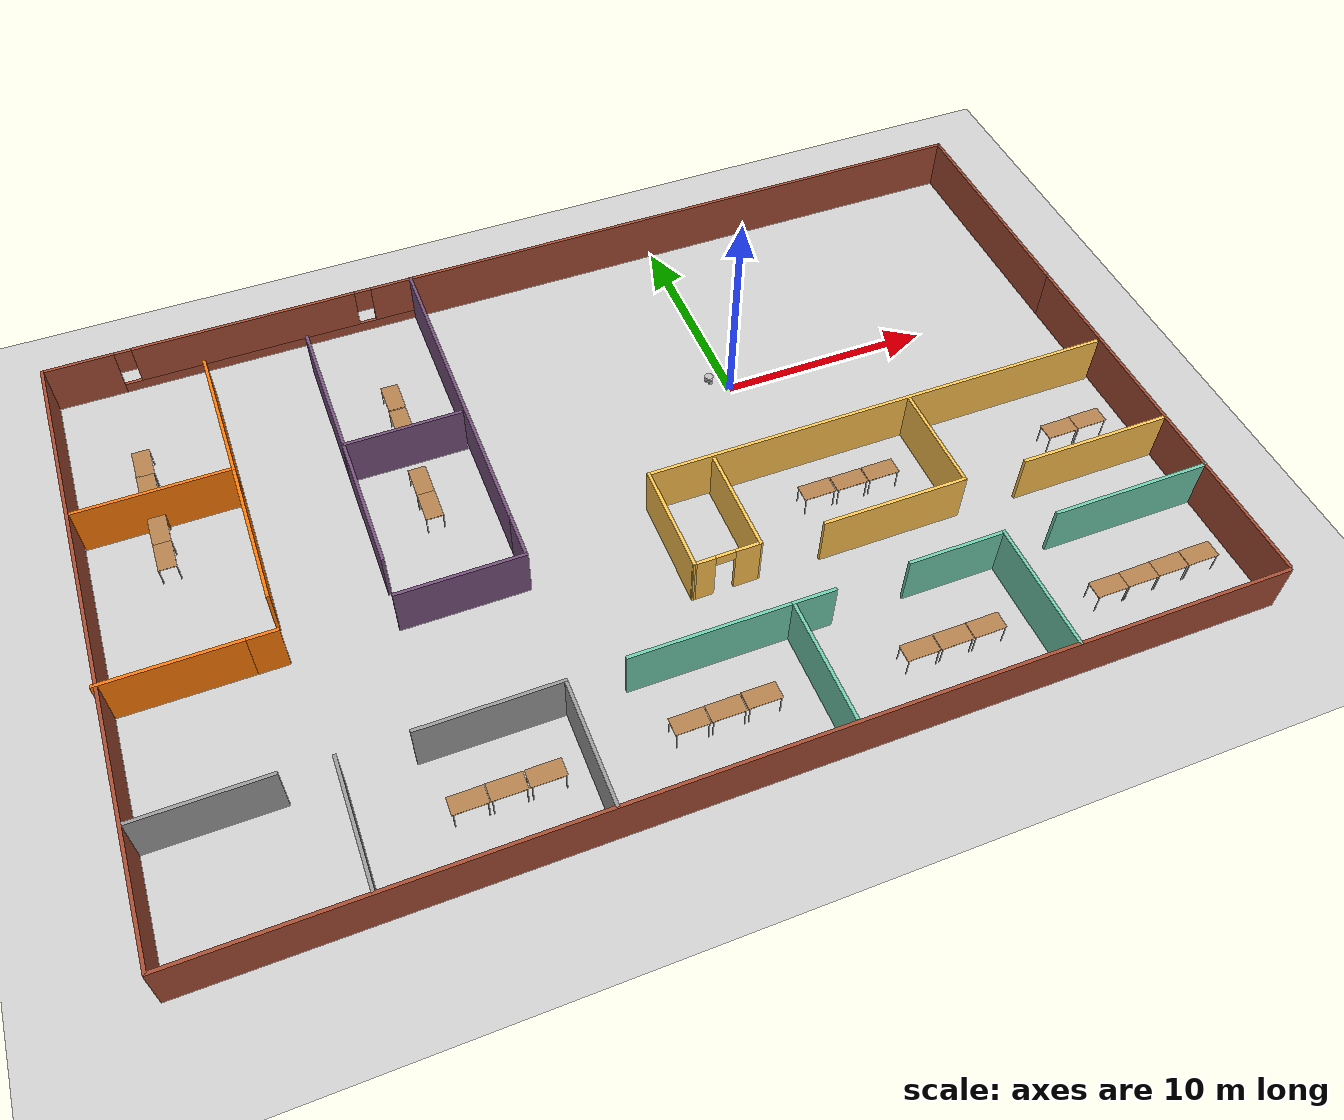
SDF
<sdf version="1.6">
 <world name="default">
  <light name="sun" type="directional">
   <pose>0 0 10 0 -0 0</pose>
   <diffuse>0.8 0.8 0.8 1</diffuse>
   <specular>0.2 0.2 0.2 1</specular>
   <attenuation>
    <range>1000</range>
    <constant>0.9</constant>
    <linear>0.01</linear>
    <quadratic>0.001</quadratic>
   </attenuation>
   <direction>-0.5 0.1 -0.9</direction>
  </light>
  <model name="ground_plane">
   <static>1</static>
   <link name="link">
    <collision name="collision">
     <geometry><plane><normal>0 0 1</normal><size>100 100</size></plane></geometry>
     <surface><friction><ode><mu>100</mu><mu2>50</mu2></ode></friction></surface>
    </collision>
    <visual name="visual">
     <cast_shadows>0</cast_shadows>
     <geometry><plane><normal>0 0 1</normal><size>100 100</size></plane></geometry>
     <material>
      <script><uri>file://media/materials/scripts/gazebo.material</uri><name>Gazebo/Grey</name></script>
     </material>
    </visual>
   </link>
  </model>
  <gravity>0 0 -9.8</gravity>
  <magnetic_field>6e-06 2.3e-05 -4.2e-05</magnetic_field>
  <atmosphere type="adiabatic"/>
  <physics name="default_physics" default="0" type="ode">
   <max_step_size>0.001</max_step_size>
   <real_time_factor>1</real_time_factor>
   <real_time_update_rate>1000</real_time_update_rate>
  </physics>
  <scene><ambient>0.4 0.4 0.4 1</ambient><background>0.7 0.7 0.7 1</background><shadows>1</shadows></scene>
  <audio><device>default</device></audio>
  <spherical_coordinates>
   <surface_model>EARTH_WGS84</surface_model>
   <latitude_deg>0</latitude_deg>
   <longitude_deg>0</longitude_deg>
   <elevation>0</elevation>
   <heading_deg>0</heading_deg>
  </spherical_coordinates>
  <model name="sinap_office">
   <pose>-6.8627 -4.6506 0 0 -0 0</pose>
   <link name="Wall_11">
    <pose>-14.3528 14.8 0 0 -0 0</pose>
    <visual name="Wall_11_Visual_0">
     <pose>-7.1066 0 1.25 0 -0 0</pose>
     <geometry><box><size>3.2868 0.15 2.5</size></box></geometry>
     <material>
      <script><uri>file://media/materials/scripts/gazebo.material</uri><name>Gazebo/Bricks</name></script>
      <ambient>1 1 1 1</ambient>
     </material>
     <meta><layer>0</layer></meta>
    </visual>
    <collision name="Wall_11_Collision_0">
     <geometry><box><size>3.2868 0.15 2.5</size></box></geometry>
     <pose>-7.1066 0 1.25 0 -0 0</pose>
    </collision>
    <visual name="Wall_11_Visual_1">
     <pose>1.6434 0 0.25 0 -0 0</pose>
     <geometry><box><size>14.2132 0.15 0.5</size></box></geometry>
     <material>
      <script><uri>file://media/materials/scripts/gazebo.material</uri><name>Gazebo/Bricks</name></script>
      <ambient>1 1 1 1</ambient>
     </material>
     <meta><layer>0</layer></meta>
    </visual>
    <collision name="Wall_11_Collision_1">
     <geometry><box><size>14.2132 0.15 0.5</size></box></geometry>
     <pose>1.6434 0 0.25 0 -0 0</pose>
    </collision>
    <visual name="Wall_11_Visual_2">
     <pose>0.608596 0 1.5 0 -0 0</pose>
     <geometry><box><size>10.5436 0.15 2</size></box></geometry>
     <material>
      <script><uri>file://media/materials/scripts/gazebo.material</uri><name>Gazebo/Bricks</name></script>
      <ambient>1 1 1 1</ambient>
     </material>
     <meta><layer>0</layer></meta>
    </visual>
    <collision name="Wall_11_Collision_2">
     <geometry><box><size>10.5436 0.15 2</size></box></geometry>
     <pose>0.608596 0 1.5 0 -0 0</pose>
    </collision>
    <visual name="Wall_11_Visual_3">
     <pose>7.71519 0 1.5 0 -0 0</pose>
     <geometry><box><size>2.06961 0.15 2</size></box></geometry>
     <material>
      <script><uri>file://media/materials/scripts/gazebo.material</uri><name>Gazebo/Bricks</name></script>
      <ambient>1 1 1 1</ambient>
     </material>
     <meta><layer>0</layer></meta>
    </visual>
    <collision name="Wall_11_Collision_3">
     <geometry><box><size>2.06961 0.15 2</size></box></geometry>
     <pose>7.71519 0 1.5 0 -0 0</pose>
    </collision>
    <visual name="Wall_11_Visual_4">
     <pose>-5.0632 0 1.9 0 -0 0</pose>
     <geometry><box><size>0.8 0.15 1.2</size></box></geometry>
     <material>
      <script><uri>file://media/materials/scripts/gazebo.material</uri><name>Gazebo/Bricks</name></script>
      <ambient>1 1 1 1</ambient>
     </material>
     <meta><layer>0</layer></meta>
    </visual>
    <collision name="Wall_11_Collision_4">
     <geometry><box><size>0.8 0.15 1.2</size></box></geometry>
     <pose>-5.0632 0 1.9 0 -0 0</pose>
    </collision>
    <visual name="Wall_11_Visual_5">
     <pose>6.28039 0 1.9 0 -0 0</pose>
     <geometry><box><size>0.8 0.15 1.2</size></box></geometry>
     <material>
      <script><uri>file://media/materials/scripts/gazebo.material</uri><name>Gazebo/Bricks</name></script>
      <ambient>1 1 1 1</ambient>
     </material>
     <meta><layer>0</layer></meta>
    </visual>
    <collision name="Wall_11_Collision_5">
     <geometry><box><size>0.8 0.15 1.2</size></box></geometry>
     <pose>6.28039 0 1.9 0 -0 0</pose>
    </collision>
   </link>
   <link name="Wall_12">
    <collision name="Wall_12_Collision">
     <geometry><box><size>15.75 0.15 2.5</size></box></geometry>
     <pose>0 0 1.25 0 -0 0</pose>
    </collision>
    <visual name="Wall_12_Visual">
     <pose>0 0 1.25 0 -0 0</pose>
     <geometry><box><size>15.75 0.15 2.5</size></box></geometry>
     <material>
      <script><uri>file://media/materials/scripts/gazebo.material</uri><name>Gazebo/Grey</name></script>
      <ambient>0.458824 0.313726 0.482353 1</ambient>
     </material>
     <meta><layer>0</layer></meta>
    </visual>
    <pose>-5.67784 7 0 0 -0 -1.5708</pose>
   </link>
   <link name="Wall_14">
    <collision name="Wall_14_Collision">
     <geometry><box><size>29 0.15 2.5</size></box></geometry>
     <pose>0 0 1.25 0 -0 0</pose>
    </collision>
    <visual name="Wall_14_Visual">
     <pose>0 0 1.25 0 -0 0</pose>
     <geometry><box><size>29 0.15 2.5</size></box></geometry>
     <material>
      <script><uri>file://media/materials/scripts/gazebo.material</uri><name>Gazebo/Bricks</name></script>
      <ambient>1 1 1 1</ambient>
     </material>
     <meta><layer>0</layer></meta>
    </visual>
    <pose>8.74716 14.8 0 0 -0 0</pose>
   </link>
   <link name="Wall_15">
    <collision name="Wall_15_Collision">
     <geometry><box><size>11 0.15 2.5</size></box></geometry>
     <pose>0 0 1.25 0 -0 0</pose>
    </collision>
    <visual name="Wall_15_Visual">
     <pose>0 0 1.25 0 -0 0</pose>
     <geometry><box><size>11 0.15 2.5</size></box></geometry>
     <material>
      <script><uri>file://media/materials/scripts/gazebo.material</uri><name>Gazebo/Bricks</name></script>
      <ambient>1 1 1 1</ambient>
     </material>
     <meta><layer>0</layer></meta>
    </visual>
    <pose>23.1722 9.375 0 0 -0 -1.5708</pose>
   </link>
   <link name="Wall_16">
    <collision name="Wall_16_Collision">
     <geometry><box><size>18.75 0.15 2.5</size></box></geometry>
     <pose>0 0 1.25 0 -0 0</pose>
    </collision>
    <visual name="Wall_16_Visual">
     <pose>0 0 1.25 0 -0 0</pose>
     <geometry><box><size>18.75 0.15 2.5</size></box></geometry>
     <material>
      <script><uri>file://media/materials/scripts/gazebo.material</uri><name>Gazebo/Bricks</name></script>
      <ambient>1 1 1 1</ambient>
     </material>
     <meta><layer>0</layer></meta>
    </visual>
    <pose>23.1722 -5.35 0 0 -0 -1.5708</pose>
   </link>
   <link name="Wall_18">
    <collision name="Wall_18_Collision">
     <geometry><box><size>46.25 0.15 2.5</size></box></geometry>
     <pose>0 0 1.25 0 -0 0</pose>
    </collision>
    <visual name="Wall_18_Visual">
     <pose>0 0 1.25 0 -0 0</pose>
     <geometry><box><size>46.25 0.15 2.5</size></box></geometry>
     <material>
      <script><uri>file://media/materials/scripts/gazebo.material</uri><name>Gazebo/Bricks</name></script>
      <ambient>0.435294 0.796078 0.67451 1</ambient>
     </material>
     <meta><layer>0</layer></meta>
    </visual>
    <pose>0.022159 -14.8 0 0 -0 0</pose>
   </link>
   <link name="Wall_22">
    <collision name="Wall_22_Collision">
     <geometry><box><size>22.5 0.15 2.5</size></box></geometry>
     <pose>0 0 1.25 0 -0 0</pose>
    </collision>
    <visual name="Wall_22_Visual">
     <pose>0 0 1.25 0 -0 0</pose>
     <geometry><box><size>22.5 0.15 2.5</size></box></geometry>
     <material>
      <script><uri>file://media/materials/scripts/gazebo.material</uri><name>Gazebo/Grey</name></script>
      <ambient>1 0.764706 0.305882 1</ambient>
     </material>
     <meta><layer>0</layer></meta>
    </visual>
    <pose>11.7514 -0.741547 0 0 -0 0</pose>
   </link>
   <link name="Wall_24">
    <collision name="Wall_24_Collision">
     <geometry><box><size>5.25 0.15 2.5</size></box></geometry>
     <pose>0 0 1.25 0 -0 0</pose>
    </collision>
    <visual name="Wall_24_Visual">
     <pose>0 0 1.25 0 -0 0</pose>
     <geometry><box><size>5.25 0.15 2.5</size></box></geometry>
     <material>
      <script><uri>file://media/materials/scripts/gazebo.material</uri><name>Gazebo/Grey</name></script>
      <ambient>1 0.764706 0.305882 1</ambient>
     </material>
     <meta><layer>0</layer></meta>
    </visual>
    <pose>0.57639 -3.29155 0 0 -0 -1.5708</pose>
   </link>
   <link name="Wall_31">
    <collision name="Wall_31_Collision">
     <geometry><box><size>2.25 0.15 2.5</size></box></geometry>
     <pose>0 0 1.25 0 -0 0</pose>
    </collision>
    <visual name="Wall_31_Visual">
     <pose>0 0 1.25 0 -0 0</pose>
     <geometry><box><size>2.25 0.15 2.5</size></box></geometry>
     <material>
      <script><uri>file://media/materials/scripts/gazebo.material</uri><name>Gazebo/Grey</name></script>
      <ambient>0.458824 0.313726 0.482353 1</ambient>
     </material>
     <meta><layer>0</layer></meta>
    </visual>
    <pose>-5.67784 -1.85 0 0 -0 -1.5708</pose>
   </link>
   <link name="Wall_34">
    <collision name="Wall_34_Collision">
     <geometry><box><size>5.75 0.15 2.5</size></box></geometry>
     <pose>0 0 1.25 0 -0 0</pose>
    </collision>
    <visual name="Wall_34_Visual">
     <pose>0 0 1.25 0 -0 0</pose>
     <geometry><box><size>5.75 0.15 2.5</size></box></geometry>
     <material>
      <script><uri>file://media/materials/scripts/gazebo.material</uri><name>Gazebo/Grey</name></script>
      <ambient>0.458824 0.313726 0.482353 1</ambient>
     </material>
     <meta><layer>0</layer></meta>
    </visual>
    <pose>-8.47784 -2.9 0 0 -0 3.14159</pose>
   </link>
   <link name="Wall_40">
    <collision name="Wall_40_Collision">
     <geometry><box><size>6 0.15 2.5</size></box></geometry>
     <pose>0 0 1.25 0 -0 0</pose>
    </collision>
    <visual name="Wall_40_Visual">
     <pose>0 0 1.25 0 -0 0</pose>
     <geometry><box><size>6 0.15 2.5</size></box></geometry>
     <material>
      <script><uri>file://media/materials/scripts/gazebo.material</uri><name>Gazebo/Grey</name></script>
      <ambient>0.996078 0.47451 0.0196078 1</ambient>
     </material>
     <meta><layer>0</layer></meta>
    </visual>
    <pose>-20.2478 -2.88015 0 0 -0 0</pose>
   </link>
   <link name="Wall_42">
    <collision name="Wall_42_Collision">
     <geometry><box><size>1.5 0.15 2.5</size></box></geometry>
     <pose>0 0 1.25 0 -0 0</pose>
    </collision>
    <visual name="Wall_42_Visual">
     <pose>0 0 1.25 0 -0 0</pose>
     <geometry><box><size>1.5 0.15 2.5</size></box></geometry>
     <material>
      <script><uri>file://media/materials/scripts/gazebo.material</uri><name>Gazebo/Grey</name></script>
      <ambient>0.996078 0.47451 0.0196078 1</ambient>
     </material>
     <meta><layer>0</layer></meta>
    </visual>
    <pose>-16.6478 -2.88015 0 0 -0 0</pose>
   </link>
   <link name="Wall_45">
    <collision name="Wall_45_Collision">
     <geometry><box><size>7 0.15 2.5</size></box></geometry>
     <pose>0 0 1.25 0 -0 0</pose>
    </collision>
    <visual name="Wall_45_Visual">
     <pose>0 0 1.25 0 -0 0</pose>
     <geometry><box><size>7 0.15 2.5</size></box></geometry>
     <material>
      <script><uri>file://media/materials/scripts/gazebo.material</uri><name>Gazebo/Grey</name></script>
      <ambient>0.996078 0.47451 0.0196078 1</ambient>
     </material>
     <meta><layer>0</layer></meta>
    </visual>
    <pose>-19.4223 5.97736 0 0 -0 3.14159</pose>
   </link>
   <link name="Wall_47">
    <collision name="Wall_47_Collision">
     <geometry><box><size>5.5 0.15 2.5</size></box></geometry>
     <pose>0 0 1.25 0 -0 0</pose>
    </collision>
    <visual name="Wall_47_Visual">
     <pose>0 0 1.25 0 -0 0</pose>
     <geometry><box><size>5.5 0.15 2.5</size></box></geometry>
     <material>
      <script><uri>file://media/materials/scripts/gazebo.material</uri><name>Gazebo/Grey</name></script>
      <ambient>0.458824 0.313726 0.482353 1</ambient>
     </material>
     <meta><layer>0</layer></meta>
    </visual>
    <pose>-8.56965 5.60305 0 0 -0 0</pose>
   </link>
   <link name="Wall_49">
    <collision name="Wall_49_Collision">
     <geometry><box><size>5 0.15 2.5</size></box></geometry>
     <pose>0 0 1.25 0 -0 0</pose>
    </collision>
    <visual name="Wall_49_Visual">
     <pose>0 0 1.25 0 -0 0</pose>
     <geometry><box><size>5 0.15 2.5</size></box></geometry>
     <material>
      <script><uri>file://media/materials/scripts/gazebo.material</uri><name>Gazebo/Grey</name></script>
      <ambient>1 0.764706 0.305882 1</ambient>
     </material>
     <meta><layer>0</layer></meta>
    </visual>
    <pose>3.54039 -3.38824 0 0 -0 1.5708</pose>
   </link>
   <link name="Wall_56">
    <collision name="Wall_56_Collision">
     <geometry><box><size>5.25 0.15 2.5</size></box></geometry>
     <pose>0 0 1.25 0 -0 0</pose>
    </collision>
    <visual name="Wall_56_Visual">
     <pose>0 0 1.25 0 -0 0</pose>
     <geometry><box><size>5.25 0.15 2.5</size></box></geometry>
     <material>
      <script><uri>file://media/materials/scripts/gazebo.material</uri><name>Gazebo/Grey</name></script>
      <ambient>1 0.764706 0.305882 1</ambient>
     </material>
     <meta><layer>0</layer></meta>
    </visual>
    <pose>13.1047 -3.29435 0 0 -0 -1.5708</pose>
   </link>
   <link name="Wall_60">
    <collision name="Wall_60_Collision">
     <geometry><box><size>5.75 0.15 2.5</size></box></geometry>
     <pose>0 0 1.25 0 -0 0</pose>
    </collision>
    <visual name="Wall_60_Visual">
     <pose>0 0 1.25 0 -0 0</pose>
     <geometry><box><size>5.75 0.15 2.5</size></box></geometry>
     <material>
      <script><uri>file://media/materials/scripts/gazebo.material</uri><name>Gazebo/Grey</name></script>
      <ambient>0.435294 0.796078 0.67451 1</ambient>
     </material>
     <meta><layer>0</layer></meta>
    </visual>
    <pose>3.52722 -11.8305 0 0 -0 -1.5708</pose>
   </link>
   <link name="Wall_62">
    <collision name="Wall_62_Collision">
     <geometry><box><size>5.75 0.15 2.5</size></box></geometry>
     <pose>0 0 1.25 0 -0 0</pose>
    </collision>
    <visual name="Wall_62_Visual">
     <pose>0 0 1.25 0 -0 0</pose>
     <geometry><box><size>5.75 0.15 2.5</size></box></geometry>
     <material>
      <script><uri>file://media/materials/scripts/gazebo.material</uri><name>Gazebo/Grey</name></script>
      <ambient>1 1 1 1</ambient>
     </material>
     <meta><layer>0</layer></meta>
    </visual>
    <pose>-6.15792 -11.9381 0 0 -0 -1.5708</pose>
   </link>
   <link name="Wall_64">
    <collision name="Wall_64_Collision">
     <geometry><box><size>5.75 0.15 2.5</size></box></geometry>
     <pose>0 0 1.25 0 -0 0</pose>
    </collision>
    <visual name="Wall_64_Visual">
     <pose>0 0 1.25 0 -0 0</pose>
     <geometry><box><size>5.75 0.15 2.5</size></box></geometry>
     <material>
      <script><uri>file://media/materials/scripts/gazebo.material</uri><name>Gazebo/Grey</name></script>
      <ambient>1 1 1 1</ambient>
     </material>
     <meta><layer>0</layer></meta>
    </visual>
    <pose>-15.1974 -11.9381 0 0 -0 -1.5708</pose>
   </link>
   <link name="Wall_66">
    <collision name="Wall_66_Collision">
     <geometry><box><size>7.25 0.15 2.5</size></box></geometry>
     <pose>0 0 1.25 0 -0 0</pose>
    </collision>
    <visual name="Wall_66_Visual">
     <pose>0 0 1.25 0 -0 0</pose>
     <geometry><box><size>7.25 0.15 2.5</size></box></geometry>
     <material>
      <script><uri>file://media/materials/scripts/gazebo.material</uri><name>Gazebo/Grey</name></script>
      <ambient>0.458824 0.313726 0.482353 1</ambient>
     </material>
     <meta><layer>0</layer></meta>
    </visual>
    <pose>-11.2446 9.15305 0 0 -0 1.5708</pose>
   </link>
   <link name="Wall_68">
    <collision name="Wall_68_Collision">
     <geometry><box><size>6.75 0.15 2.5</size></box></geometry>
     <pose>0 0 1.25 0 -0 0</pose>
    </collision>
    <visual name="Wall_68_Visual">
     <pose>0 0 1.25 0 -0 0</pose>
     <geometry><box><size>6.75 0.15 2.5</size></box></geometry>
     <material>
      <script><uri>file://media/materials/scripts/gazebo.material</uri><name>Gazebo/Grey</name></script>
      <ambient>0.458824 0.313726 0.482353 1</ambient>
     </material>
     <meta><layer>0</layer></meta>
    </visual>
    <pose>-11.2446 2.30305 0 0 -0 -1.5708</pose>
   </link>
   <link name="Wall_70">
    <collision name="Wall_70_Collision">
     <geometry><box><size>7.25003 0.15 2.5</size></box></geometry>
     <pose>0 0 1.25 0 -0 0</pose>
    </collision>
    <visual name="Wall_70_Visual">
     <pose>0 0 1.25 0 -0 0</pose>
     <geometry><box><size>7.25003 0.15 2.5</size></box></geometry>
     <material>
      <script><uri>file://media/materials/scripts/gazebo.material</uri><name>Gazebo/Grey</name></script>
      <ambient>0.996078 0.47451 0.0196078 1</ambient>
     </material>
     <meta><layer>0</layer></meta>
    </visual>
    <pose>-16.0071 2.42736 0 0 -0 -1.57358</pose>
   </link>
   <link name="Wall_72">
    <collision name="Wall_72_Collision">
     <geometry><box><size>7 0.15 2.5</size></box></geometry>
     <pose>0 0 1.25 0 -0 0</pose>
    </collision>
    <visual name="Wall_72_Visual">
     <pose>0 0 1.25 0 -0 0</pose>
     <geometry><box><size>7 0.15 2.5</size></box></geometry>
     <material>
      <script><uri>file://media/materials/scripts/gazebo.material</uri><name>Gazebo/Grey</name></script>
      <ambient>0.996078 0.47451 0.0196078 1</ambient>
     </material>
     <meta><layer>0</layer></meta>
    </visual>
    <pose>-15.9973 9.38258 0 0 -0 1.5708</pose>
   </link>
   <link name="Wall_74">
    <collision name="Wall_74_Collision">
     <geometry><box><size>5.75 0.15 2.5</size></box></geometry>
     <pose>0 0 1.25 0 -0 0</pose>
    </collision>
    <visual name="Wall_74_Visual">
     <pose>0 0 1.25 0 -0 0</pose>
     <geometry><box><size>5.75 0.15 2.5</size></box></geometry>
     <material>
      <script><uri>file://media/materials/scripts/gazebo.material</uri><name>Gazebo/Grey</name></script>
      <ambient>1 1 1 1</ambient>
     </material>
     <meta><layer>0</layer></meta>
    </visual>
    <pose>-20.1768 -9.05523 0 0 -0 0</pose>
   </link>
   <link name="Wall_76">
    <collision name="Wall_76_Collision">
     <geometry><box><size>6.25 0.15 2.5</size></box></geometry>
     <pose>0 0 1.25 0 -0 0</pose>
    </collision>
    <visual name="Wall_76_Visual">
     <pose>0 0 1.25 0 -0 0</pose>
     <geometry><box><size>6.25 0.15 2.5</size></box></geometry>
     <material>
      <script><uri>file://media/materials/scripts/gazebo.material</uri><name>Gazebo/Grey</name></script>
      <ambient>1 1 1 1</ambient>
     </material>
     <meta><layer>0</layer></meta>
    </visual>
    <pose>-9.20792 -9.13814 0 0 -0 3.14159</pose>
   </link>
   <link name="Wall_78">
    <collision name="Wall_78_Collision">
     <geometry><box><size>7.25 0.15 2.5</size></box></geometry>
     <pose>0 0 1.25 0 -0 0</pose>
    </collision>
    <visual name="Wall_78_Visual">
     <pose>0 0 1.25 0 -0 0</pose>
     <geometry><box><size>7.25 0.15 2.5</size></box></geometry>
     <material>
      <script><uri>file://media/materials/scripts/gazebo.material</uri><name>Gazebo/Grey</name></script>
      <ambient>0.435294 0.796078 0.67451 1</ambient>
     </material>
     <meta><layer>0</layer></meta>
    </visual>
    <pose>-0.022782 -9.03053 0 0 -0 3.14159</pose>
   </link>
   <link name="Wall_80">
    <collision name="Wall_80_Collision">
     <geometry><box><size>2 0.15 2.5</size></box></geometry>
     <pose>0 0 1.25 0 -0 0</pose>
    </collision>
    <visual name="Wall_80_Visual">
     <pose>0 0 1.25 0 -0 0</pose>
     <geometry><box><size>2 0.15 2.5</size></box></geometry>
     <material>
      <script><uri>file://media/materials/scripts/gazebo.material</uri><name>Gazebo/Grey</name></script>
      <ambient>0.435294 0.796078 0.67451 1</ambient>
     </material>
     <meta><layer>0</layer></meta>
    </visual>
    <pose>4.45222 -9.03053 0 0 -0 0</pose>
   </link>
   <link name="Wall_83">
    <collision name="Wall_83_Collision">
     <geometry><box><size>4.5 0.15 2.5</size></box></geometry>
     <pose>0 0 1.25 0 -0 0</pose>
    </collision>
    <visual name="Wall_83_Visual">
     <pose>0 0 1.25 0 -0 0</pose>
     <geometry><box><size>4.5 0.15 2.5</size></box></geometry>
     <material>
      <script><uri>file://media/materials/scripts/gazebo.material</uri><name>Gazebo/Grey</name></script>
      <ambient>0.435294 0.796078 0.67451 1</ambient>
     </material>
     <meta><layer>0</layer></meta>
    </visual>
    <pose>11.0308 -8.93741 0 0 -0 0</pose>
   </link>
   <link name="Wall_84">
    <collision name="Wall_84_Collision">
     <geometry><box><size>6 0.15 2.5</size></box></geometry>
     <pose>0 0 1.25 0 -0 0</pose>
    </collision>
    <visual name="Wall_84_Visual">
     <pose>0 0 1.25 0 -0 0</pose>
     <geometry><box><size>6 0.15 2.5</size></box></geometry>
     <material>
      <script><uri>file://media/materials/scripts/gazebo.material</uri><name>Gazebo/Grey</name></script>
      <ambient>0.435294 0.796078 0.67451 1</ambient>
     </material>
     <meta><layer>0</layer></meta>
    </visual>
    <pose>13.2058 -11.8624 0 0 -0 -1.5708</pose>
   </link>
   <link name="Wall_86">
    <collision name="Wall_86_Collision">
     <geometry><box><size>7.25 0.15 2.5</size></box></geometry>
     <pose>0 0 1.25 0 -0 0</pose>
    </collision>
    <visual name="Wall_86_Visual">
     <pose>0 0 1.25 0 -0 0</pose>
     <geometry><box><size>7.25 0.15 2.5</size></box></geometry>
     <material>
      <script><uri>file://media/materials/scripts/gazebo.material</uri><name>Gazebo/Grey</name></script>
      <ambient>1 0.764706 0.305882 1</ambient>
     </material>
     <meta><layer>0</layer></meta>
    </visual>
    <pose>19.6228 -5.9023 0 0 -0 3.14159</pose>
   </link>
   <link name="Wall_88">
    <collision name="Wall_88_Collision">
     <geometry><box><size>7.5 0.15 2.5</size></box></geometry>
     <pose>0 0 1.25 0 -0 0</pose>
    </collision>
    <visual name="Wall_88_Visual">
     <pose>0 0 1.25 0 -0 0</pose>
     <geometry><box><size>7.5 0.15 2.5</size></box></geometry>
     <material>
      <script><uri>file://media/materials/scripts/gazebo.material</uri><name>Gazebo/Grey</name></script>
      <ambient>0.435294 0.796078 0.67451 1</ambient>
     </material>
     <meta><layer>0</layer></meta>
    </visual>
    <pose>19.4978 -8.8647 0 0 -0 3.14159</pose>
   </link>
   <link name="Wall_9">
    <collision name="Wall_9_Collision">
     <geometry><box><size>29.75 0.15 2.5</size></box></geometry>
     <pose>0 0 1.25 0 -0 0</pose>
    </collision>
    <visual name="Wall_9_Visual">
     <pose>0 0 1.25 0 -0 0</pose>
     <geometry><box><size>29.75 0.15 2.5</size></box></geometry>
     <material>
      <script><uri>file://media/materials/scripts/gazebo.material</uri><name>Gazebo/Bricks</name></script>
      <ambient>1 1 1 1</ambient>
     </material>
     <meta><layer>0</layer></meta>
    </visual>
    <pose>-23.0278 0 0 0 -0 -1.5708</pose>
   </link>
   <link name="Wall_91">
    <collision name="Wall_91_Collision">
     <geometry><box><size>6.75 0.15 2.5</size></box></geometry>
     <pose>0 0 1.25 0 -0 0</pose>
    </collision>
    <visual name="Wall_91_Visual">
     <pose>0 0 1.25 0 -0 0</pose>
     <geometry><box><size>6.75 0.15 2.5</size></box></geometry>
     <material>
      <script><uri>file://media/materials/scripts/gazebo.material</uri><name>Gazebo/Grey</name></script>
      <ambient>1 0.764706 0.305882 1</ambient>
     </material>
     <meta><layer>0</layer></meta>
    </visual>
    <pose>9.80474 -5.84436 0 0 -0 3.14159</pose>
   </link>
   <link name="Wall_93">
    <pose>2.05839 -5.8274 0 0 -0 0.009549</pose>
    <visual name="Wall_93_Visual_0">
     <pose>-1.05491 0 1.25 0 -0 0</pose>
     <geometry><box><size>1.00432 0.15 2.5</size></box></geometry>
     <material>
      <script><uri>file://media/materials/scripts/gazebo.material</uri><name>Gazebo/Grey</name></script>
      <ambient>1 0.764706 0.305882 1</ambient>
     </material>
     <meta><layer>0</layer></meta>
    </visual>
    <collision name="Wall_93_Collision_0">
     <geometry><box><size>1.00432 0.15 2.5</size></box></geometry>
     <pose>-1.05491 0 1.25 0 -0 0</pose>
    </collision>
    <visual name="Wall_93_Visual_1">
     <pose>0.95216 0 1.25 0 -0 0</pose>
     <geometry><box><size>1.20982 0.15 2.5</size></box></geometry>
     <material>
      <script><uri>file://media/materials/scripts/gazebo.material</uri><name>Gazebo/Grey</name></script>
      <ambient>1 0.764706 0.305882 1</ambient>
     </material>
     <meta><layer>0</layer></meta>
    </visual>
    <collision name="Wall_93_Collision_1">
     <geometry><box><size>1.20982 0.15 2.5</size></box></geometry>
     <pose>0.95216 0 1.25 0 -0 0</pose>
    </collision>
    <visual name="Wall_93_Visual_2">
     <pose>-0.102748 0 2.25 0 -0 0</pose>
     <geometry><box><size>0.9 0.15 0.5</size></box></geometry>
     <material>
      <script><uri>file://media/materials/scripts/gazebo.material</uri><name>Gazebo/Grey</name></script>
      <ambient>1 0.764706 0.305882 1</ambient>
     </material>
     <meta><layer>0</layer></meta>
    </visual>
    <collision name="Wall_93_Collision_2">
     <geometry><box><size>0.9 0.15 0.5</size></box></geometry>
     <pose>-0.102748 0 2.25 0 -0 0</pose>
    </collision>
   </link>
   <static>1</static>
  </model>
  <model name="table">
   <static>1</static>
   <link name="link">
    <collision name="surface">
     <pose>0 0 1 0 -0 0</pose>
     <geometry><box><size>1.5 0.8 0.03</size></box></geometry>
     <surface><friction><ode><mu>0.6</mu><mu2>0.6</mu2></ode></friction></surface>
    </collision>
    <visual name="visual1">
     <pose>0 0 1 0 -0 0</pose>
     <geometry><box><size>1.5 0.8 0.03</size></box></geometry>
     <material>
      <script><uri>file://media/materials/scripts/gazebo.material</uri><name>Gazebo/Wood</name></script>
     </material>
    </visual>
    <collision name="front_left_leg">
     <pose>0.68 0.38 0.5 0 -0 0</pose>
     <geometry><cylinder><radius>0.02</radius><length>1</length></cylinder></geometry>
    </collision>
    <visual name="front_left_leg">
     <pose>0.68 0.38 0.5 0 -0 0</pose>
     <geometry><cylinder><radius>0.02</radius><length>1</length></cylinder></geometry>
     <material>
      <script><uri>file://media/materials/scripts/gazebo.material</uri><name>Gazebo/Grey</name></script>
     </material>
    </visual>
    <collision name="front_right_leg">
     <pose>0.68 -0.38 0.5 0 -0 0</pose>
     <geometry><cylinder><radius>0.02</radius><length>1</length></cylinder></geometry>
    </collision>
    <visual name="front_right_leg">
     <pose>0.68 -0.38 0.5 0 -0 0</pose>
     <geometry><cylinder><radius>0.02</radius><length>1</length></cylinder></geometry>
     <material>
      <script><uri>file://media/materials/scripts/gazebo.material</uri><name>Gazebo/Grey</name></script>
     </material>
    </visual>
    <collision name="back_right_leg">
     <pose>-0.68 -0.38 0.5 0 -0 0</pose>
     <geometry><cylinder><radius>0.02</radius><length>1</length></cylinder></geometry>
    </collision>
    <visual name="back_right_leg">
     <pose>-0.68 -0.38 0.5 0 -0 0</pose>
     <geometry><cylinder><radius>0.02</radius><length>1</length></cylinder></geometry>
     <material>
      <script><uri>file://media/materials/scripts/gazebo.material</uri><name>Gazebo/Grey</name></script>
     </material>
    </visual>
    <collision name="back_left_leg">
     <pose>-0.68 0.38 0.5 0 -0 0</pose>
     <geometry><cylinder><radius>0.02</radius><length>1</length></cylinder></geometry>
    </collision>
    <visual name="back_left_leg">
     <pose>-0.68 0.38 0.5 0 -0 0</pose>
     <geometry><cylinder><radius>0.02</radius><length>1</length></cylinder></geometry>
     <material>
      <script><uri>file://media/materials/scripts/gazebo.material</uri><name>Gazebo/Grey</name></script>
     </material>
    </visual>
   </link>
   <pose>14.0819 -8.38922 0 0 -0 0</pose>
  </model>
  <model name="table_clone">
   <static>1</static>
   <link name="link">
    <collision name="surface">
     <pose>0 0 1 0 -0 0</pose>
     <geometry><box><size>1.5 0.8 0.03</size></box></geometry>
     <surface><friction><ode><mu>0.6</mu><mu2>0.6</mu2></ode></friction></surface>
    </collision>
    <visual name="visual1">
     <pose>0 0 1 0 -0 0</pose>
     <geometry><box><size>1.5 0.8 0.03</size></box></geometry>
     <material>
      <script><uri>file://media/materials/scripts/gazebo.material</uri><name>Gazebo/Wood</name></script>
     </material>
    </visual>
    <collision name="front_left_leg">
     <pose>0.68 0.38 0.5 0 -0 0</pose>
     <geometry><cylinder><radius>0.02</radius><length>1</length></cylinder></geometry>
    </collision>
    <visual name="front_left_leg">
     <pose>0.68 0.38 0.5 0 -0 0</pose>
     <geometry><cylinder><radius>0.02</radius><length>1</length></cylinder></geometry>
     <material>
      <script><uri>file://media/materials/scripts/gazebo.material</uri><name>Gazebo/Grey</name></script>
     </material>
    </visual>
    <collision name="front_right_leg">
     <pose>0.68 -0.38 0.5 0 -0 0</pose>
     <geometry><cylinder><radius>0.02</radius><length>1</length></cylinder></geometry>
    </collision>
    <visual name="front_right_leg">
     <pose>0.68 -0.38 0.5 0 -0 0</pose>
     <geometry><cylinder><radius>0.02</radius><length>1</length></cylinder></geometry>
     <material>
      <script><uri>file://media/materials/scripts/gazebo.material</uri><name>Gazebo/Grey</name></script>
     </material>
    </visual>
    <collision name="back_right_leg">
     <pose>-0.68 -0.38 0.5 0 -0 0</pose>
     <geometry><cylinder><radius>0.02</radius><length>1</length></cylinder></geometry>
    </collision>
    <visual name="back_right_leg">
     <pose>-0.68 -0.38 0.5 0 -0 0</pose>
     <geometry><cylinder><radius>0.02</radius><length>1</length></cylinder></geometry>
     <material>
      <script><uri>file://media/materials/scripts/gazebo.material</uri><name>Gazebo/Grey</name></script>
     </material>
    </visual>
    <collision name="back_left_leg">
     <pose>-0.68 0.38 0.5 0 -0 0</pose>
     <geometry><cylinder><radius>0.02</radius><length>1</length></cylinder></geometry>
    </collision>
    <visual name="back_left_leg">
     <pose>-0.68 0.38 0.5 0 -0 0</pose>
     <geometry><cylinder><radius>0.02</radius><length>1</length></cylinder></geometry>
     <material>
      <script><uri>file://media/materials/scripts/gazebo.material</uri><name>Gazebo/Grey</name></script>
     </material>
    </visual>
   </link>
   <pose>12.5791 -8.42531 0 0 -0 0</pose>
  </model>
  <model name="table_clone_0">
   <static>1</static>
   <link name="link">
    <collision name="surface">
     <pose>0 0 1 0 -0 0</pose>
     <geometry><box><size>1.5 0.8 0.03</size></box></geometry>
     <surface><friction><ode><mu>0.6</mu><mu2>0.6</mu2></ode></friction></surface>
    </collision>
    <visual name="visual1">
     <pose>0 0 1 0 -0 0</pose>
     <geometry><box><size>1.5 0.8 0.03</size></box></geometry>
     <material>
      <script><uri>file://media/materials/scripts/gazebo.material</uri><name>Gazebo/Wood</name></script>
     </material>
    </visual>
    <collision name="front_left_leg">
     <pose>0.68 0.38 0.5 0 -0 0</pose>
     <geometry><cylinder><radius>0.02</radius><length>1</length></cylinder></geometry>
    </collision>
    <visual name="front_left_leg">
     <pose>0.68 0.38 0.5 0 -0 0</pose>
     <geometry><cylinder><radius>0.02</radius><length>1</length></cylinder></geometry>
     <material>
      <script><uri>file://media/materials/scripts/gazebo.material</uri><name>Gazebo/Grey</name></script>
     </material>
    </visual>
    <collision name="front_right_leg">
     <pose>0.68 -0.38 0.5 0 -0 0</pose>
     <geometry><cylinder><radius>0.02</radius><length>1</length></cylinder></geometry>
    </collision>
    <visual name="front_right_leg">
     <pose>0.68 -0.38 0.5 0 -0 0</pose>
     <geometry><cylinder><radius>0.02</radius><length>1</length></cylinder></geometry>
     <material>
      <script><uri>file://media/materials/scripts/gazebo.material</uri><name>Gazebo/Grey</name></script>
     </material>
    </visual>
    <collision name="back_right_leg">
     <pose>-0.68 -0.38 0.5 0 -0 0</pose>
     <geometry><cylinder><radius>0.02</radius><length>1</length></cylinder></geometry>
    </collision>
    <visual name="back_right_leg">
     <pose>-0.68 -0.38 0.5 0 -0 0</pose>
     <geometry><cylinder><radius>0.02</radius><length>1</length></cylinder></geometry>
     <material>
      <script><uri>file://media/materials/scripts/gazebo.material</uri><name>Gazebo/Grey</name></script>
     </material>
    </visual>
    <collision name="back_left_leg">
     <pose>-0.68 0.38 0.5 0 -0 0</pose>
     <geometry><cylinder><radius>0.02</radius><length>1</length></cylinder></geometry>
    </collision>
    <visual name="back_left_leg">
     <pose>-0.68 0.38 0.5 0 -0 0</pose>
     <geometry><cylinder><radius>0.02</radius><length>1</length></cylinder></geometry>
     <material>
      <script><uri>file://media/materials/scripts/gazebo.material</uri><name>Gazebo/Grey</name></script>
     </material>
    </visual>
   </link>
   <pose>14.2864 -16.6612 0 0 -0 0</pose>
  </model>
  <model name="table_clone_1">
   <static>1</static>
   <link name="link">
    <collision name="surface">
     <pose>0 0 1 0 -0 0</pose>
     <geometry><box><size>1.5 0.8 0.03</size></box></geometry>
     <surface><friction><ode><mu>0.6</mu><mu2>0.6</mu2></ode></friction></surface>
    </collision>
    <visual name="visual1">
     <pose>0 0 1 0 -0 0</pose>
     <geometry><box><size>1.5 0.8 0.03</size></box></geometry>
     <material>
      <script><uri>file://media/materials/scripts/gazebo.material</uri><name>Gazebo/Wood</name></script>
     </material>
    </visual>
    <collision name="front_left_leg">
     <pose>0.68 0.38 0.5 0 -0 0</pose>
     <geometry><cylinder><radius>0.02</radius><length>1</length></cylinder></geometry>
    </collision>
    <visual name="front_left_leg">
     <pose>0.68 0.38 0.5 0 -0 0</pose>
     <geometry><cylinder><radius>0.02</radius><length>1</length></cylinder></geometry>
     <material>
      <script><uri>file://media/materials/scripts/gazebo.material</uri><name>Gazebo/Grey</name></script>
     </material>
    </visual>
    <collision name="front_right_leg">
     <pose>0.68 -0.38 0.5 0 -0 0</pose>
     <geometry><cylinder><radius>0.02</radius><length>1</length></cylinder></geometry>
    </collision>
    <visual name="front_right_leg">
     <pose>0.68 -0.38 0.5 0 -0 0</pose>
     <geometry><cylinder><radius>0.02</radius><length>1</length></cylinder></geometry>
     <material>
      <script><uri>file://media/materials/scripts/gazebo.material</uri><name>Gazebo/Grey</name></script>
     </material>
    </visual>
    <collision name="back_right_leg">
     <pose>-0.68 -0.38 0.5 0 -0 0</pose>
     <geometry><cylinder><radius>0.02</radius><length>1</length></cylinder></geometry>
    </collision>
    <visual name="back_right_leg">
     <pose>-0.68 -0.38 0.5 0 -0 0</pose>
     <geometry><cylinder><radius>0.02</radius><length>1</length></cylinder></geometry>
     <material>
      <script><uri>file://media/materials/scripts/gazebo.material</uri><name>Gazebo/Grey</name></script>
     </material>
    </visual>
    <collision name="back_left_leg">
     <pose>-0.68 0.38 0.5 0 -0 0</pose>
     <geometry><cylinder><radius>0.02</radius><length>1</length></cylinder></geometry>
    </collision>
    <visual name="back_left_leg">
     <pose>-0.68 0.38 0.5 0 -0 0</pose>
     <geometry><cylinder><radius>0.02</radius><length>1</length></cylinder></geometry>
     <material>
      <script><uri>file://media/materials/scripts/gazebo.material</uri><name>Gazebo/Grey</name></script>
     </material>
    </visual>
   </link>
   <pose>12.7739 -16.685 0 0 -0 0</pose>
  </model>
  <model name="table_clone_2">
   <static>1</static>
   <link name="link">
    <collision name="surface">
     <pose>0 0 1 0 -0 0</pose>
     <geometry><box><size>1.5 0.8 0.03</size></box></geometry>
     <surface><friction><ode><mu>0.6</mu><mu2>0.6</mu2></ode></friction></surface>
    </collision>
    <visual name="visual1">
     <pose>0 0 1 0 -0 0</pose>
     <geometry><box><size>1.5 0.8 0.03</size></box></geometry>
     <material>
      <script><uri>file://media/materials/scripts/gazebo.material</uri><name>Gazebo/Wood</name></script>
     </material>
    </visual>
    <collision name="front_left_leg">
     <pose>0.68 0.38 0.5 0 -0 0</pose>
     <geometry><cylinder><radius>0.02</radius><length>1</length></cylinder></geometry>
    </collision>
    <visual name="front_left_leg">
     <pose>0.68 0.38 0.5 0 -0 0</pose>
     <geometry><cylinder><radius>0.02</radius><length>1</length></cylinder></geometry>
     <material>
      <script><uri>file://media/materials/scripts/gazebo.material</uri><name>Gazebo/Grey</name></script>
     </material>
    </visual>
    <collision name="front_right_leg">
     <pose>0.68 -0.38 0.5 0 -0 0</pose>
     <geometry><cylinder><radius>0.02</radius><length>1</length></cylinder></geometry>
    </collision>
    <visual name="front_right_leg">
     <pose>0.68 -0.38 0.5 0 -0 0</pose>
     <geometry><cylinder><radius>0.02</radius><length>1</length></cylinder></geometry>
     <material>
      <script><uri>file://media/materials/scripts/gazebo.material</uri><name>Gazebo/Grey</name></script>
     </material>
    </visual>
    <collision name="back_right_leg">
     <pose>-0.68 -0.38 0.5 0 -0 0</pose>
     <geometry><cylinder><radius>0.02</radius><length>1</length></cylinder></geometry>
    </collision>
    <visual name="back_right_leg">
     <pose>-0.68 -0.38 0.5 0 -0 0</pose>
     <geometry><cylinder><radius>0.02</radius><length>1</length></cylinder></geometry>
     <material>
      <script><uri>file://media/materials/scripts/gazebo.material</uri><name>Gazebo/Grey</name></script>
     </material>
    </visual>
    <collision name="back_left_leg">
     <pose>-0.68 0.38 0.5 0 -0 0</pose>
     <geometry><cylinder><radius>0.02</radius><length>1</length></cylinder></geometry>
    </collision>
    <visual name="back_left_leg">
     <pose>-0.68 0.38 0.5 0 -0 0</pose>
     <geometry><cylinder><radius>0.02</radius><length>1</length></cylinder></geometry>
     <material>
      <script><uri>file://media/materials/scripts/gazebo.material</uri><name>Gazebo/Grey</name></script>
     </material>
    </visual>
   </link>
   <pose>11.2999 -16.7016 0 0 -0 0</pose>
  </model>
  <model name="table_clone_3">
   <static>1</static>
   <link name="link">
    <collision name="surface">
     <pose>0 0 1 0 -0 0</pose>
     <geometry><box><size>1.5 0.8 0.03</size></box></geometry>
     <surface><friction><ode><mu>0.6</mu><mu2>0.6</mu2></ode></friction></surface>
    </collision>
    <visual name="visual1">
     <pose>0 0 1 0 -0 0</pose>
     <geometry><box><size>1.5 0.8 0.03</size></box></geometry>
     <material>
      <script><uri>file://media/materials/scripts/gazebo.material</uri><name>Gazebo/Wood</name></script>
     </material>
    </visual>
    <collision name="front_left_leg">
     <pose>0.68 0.38 0.5 0 -0 0</pose>
     <geometry><cylinder><radius>0.02</radius><length>1</length></cylinder></geometry>
    </collision>
    <visual name="front_left_leg">
     <pose>0.68 0.38 0.5 0 -0 0</pose>
     <geometry><cylinder><radius>0.02</radius><length>1</length></cylinder></geometry>
     <material>
      <script><uri>file://media/materials/scripts/gazebo.material</uri><name>Gazebo/Grey</name></script>
     </material>
    </visual>
    <collision name="front_right_leg">
     <pose>0.68 -0.38 0.5 0 -0 0</pose>
     <geometry><cylinder><radius>0.02</radius><length>1</length></cylinder></geometry>
    </collision>
    <visual name="front_right_leg">
     <pose>0.68 -0.38 0.5 0 -0 0</pose>
     <geometry><cylinder><radius>0.02</radius><length>1</length></cylinder></geometry>
     <material>
      <script><uri>file://media/materials/scripts/gazebo.material</uri><name>Gazebo/Grey</name></script>
     </material>
    </visual>
    <collision name="back_right_leg">
     <pose>-0.68 -0.38 0.5 0 -0 0</pose>
     <geometry><cylinder><radius>0.02</radius><length>1</length></cylinder></geometry>
    </collision>
    <visual name="back_right_leg">
     <pose>-0.68 -0.38 0.5 0 -0 0</pose>
     <geometry><cylinder><radius>0.02</radius><length>1</length></cylinder></geometry>
     <material>
      <script><uri>file://media/materials/scripts/gazebo.material</uri><name>Gazebo/Grey</name></script>
     </material>
    </visual>
    <collision name="back_left_leg">
     <pose>-0.68 0.38 0.5 0 -0 0</pose>
     <geometry><cylinder><radius>0.02</radius><length>1</length></cylinder></geometry>
    </collision>
    <visual name="back_left_leg">
     <pose>-0.68 0.38 0.5 0 -0 0</pose>
     <geometry><cylinder><radius>0.02</radius><length>1</length></cylinder></geometry>
     <material>
      <script><uri>file://media/materials/scripts/gazebo.material</uri><name>Gazebo/Grey</name></script>
     </material>
    </visual>
   </link>
   <pose>9.83498 -16.7133 0 0 -0 0</pose>
  </model>
  <model name="table_clone_4">
   <static>1</static>
   <link name="link">
    <collision name="surface">
     <pose>0 0 1 0 -0 0</pose>
     <geometry><box><size>1.5 0.8 0.03</size></box></geometry>
     <surface><friction><ode><mu>0.6</mu><mu2>0.6</mu2></ode></friction></surface>
    </collision>
    <visual name="visual1">
     <pose>0 0 1 0 -0 0</pose>
     <geometry><box><size>1.5 0.8 0.03</size></box></geometry>
     <material>
      <script><uri>file://media/materials/scripts/gazebo.material</uri><name>Gazebo/Wood</name></script>
     </material>
    </visual>
    <collision name="front_left_leg">
     <pose>0.68 0.38 0.5 0 -0 0</pose>
     <geometry><cylinder><radius>0.02</radius><length>1</length></cylinder></geometry>
    </collision>
    <visual name="front_left_leg">
     <pose>0.68 0.38 0.5 0 -0 0</pose>
     <geometry><cylinder><radius>0.02</radius><length>1</length></cylinder></geometry>
     <material>
      <script><uri>file://media/materials/scripts/gazebo.material</uri><name>Gazebo/Grey</name></script>
     </material>
    </visual>
    <collision name="front_right_leg">
     <pose>0.68 -0.38 0.5 0 -0 0</pose>
     <geometry><cylinder><radius>0.02</radius><length>1</length></cylinder></geometry>
    </collision>
    <visual name="front_right_leg">
     <pose>0.68 -0.38 0.5 0 -0 0</pose>
     <geometry><cylinder><radius>0.02</radius><length>1</length></cylinder></geometry>
     <material>
      <script><uri>file://media/materials/scripts/gazebo.material</uri><name>Gazebo/Grey</name></script>
     </material>
    </visual>
    <collision name="back_right_leg">
     <pose>-0.68 -0.38 0.5 0 -0 0</pose>
     <geometry><cylinder><radius>0.02</radius><length>1</length></cylinder></geometry>
    </collision>
    <visual name="back_right_leg">
     <pose>-0.68 -0.38 0.5 0 -0 0</pose>
     <geometry><cylinder><radius>0.02</radius><length>1</length></cylinder></geometry>
     <material>
      <script><uri>file://media/materials/scripts/gazebo.material</uri><name>Gazebo/Grey</name></script>
     </material>
    </visual>
    <collision name="back_left_leg">
     <pose>-0.68 0.38 0.5 0 -0 0</pose>
     <geometry><cylinder><radius>0.02</radius><length>1</length></cylinder></geometry>
    </collision>
    <visual name="back_left_leg">
     <pose>-0.68 0.38 0.5 0 -0 0</pose>
     <geometry><cylinder><radius>0.02</radius><length>1</length></cylinder></geometry>
     <material>
      <script><uri>file://media/materials/scripts/gazebo.material</uri><name>Gazebo/Grey</name></script>
     </material>
    </visual>
   </link>
   <pose>4.07121 -16.6152 0 0 -0 0</pose>
  </model>
  <model name="table_clone_5">
   <static>1</static>
   <link name="link">
    <collision name="surface">
     <pose>0 0 1 0 -0 0</pose>
     <geometry><box><size>1.5 0.8 0.03</size></box></geometry>
     <surface><friction><ode><mu>0.6</mu><mu2>0.6</mu2></ode></friction></surface>
    </collision>
    <visual name="visual1">
     <pose>0 0 1 0 -0 0</pose>
     <geometry><box><size>1.5 0.8 0.03</size></box></geometry>
     <material>
      <script><uri>file://media/materials/scripts/gazebo.material</uri><name>Gazebo/Wood</name></script>
     </material>
    </visual>
    <collision name="front_left_leg">
     <pose>0.68 0.38 0.5 0 -0 0</pose>
     <geometry><cylinder><radius>0.02</radius><length>1</length></cylinder></geometry>
    </collision>
    <visual name="front_left_leg">
     <pose>0.68 0.38 0.5 0 -0 0</pose>
     <geometry><cylinder><radius>0.02</radius><length>1</length></cylinder></geometry>
     <material>
      <script><uri>file://media/materials/scripts/gazebo.material</uri><name>Gazebo/Grey</name></script>
     </material>
    </visual>
    <collision name="front_right_leg">
     <pose>0.68 -0.38 0.5 0 -0 0</pose>
     <geometry><cylinder><radius>0.02</radius><length>1</length></cylinder></geometry>
    </collision>
    <visual name="front_right_leg">
     <pose>0.68 -0.38 0.5 0 -0 0</pose>
     <geometry><cylinder><radius>0.02</radius><length>1</length></cylinder></geometry>
     <material>
      <script><uri>file://media/materials/scripts/gazebo.material</uri><name>Gazebo/Grey</name></script>
     </material>
    </visual>
    <collision name="back_right_leg">
     <pose>-0.68 -0.38 0.5 0 -0 0</pose>
     <geometry><cylinder><radius>0.02</radius><length>1</length></cylinder></geometry>
    </collision>
    <visual name="back_right_leg">
     <pose>-0.68 -0.38 0.5 0 -0 0</pose>
     <geometry><cylinder><radius>0.02</radius><length>1</length></cylinder></geometry>
     <material>
      <script><uri>file://media/materials/scripts/gazebo.material</uri><name>Gazebo/Grey</name></script>
     </material>
    </visual>
    <collision name="back_left_leg">
     <pose>-0.68 0.38 0.5 0 -0 0</pose>
     <geometry><cylinder><radius>0.02</radius><length>1</length></cylinder></geometry>
    </collision>
    <visual name="back_left_leg">
     <pose>-0.68 0.38 0.5 0 -0 0</pose>
     <geometry><cylinder><radius>0.02</radius><length>1</length></cylinder></geometry>
     <material>
      <script><uri>file://media/materials/scripts/gazebo.material</uri><name>Gazebo/Grey</name></script>
     </material>
    </visual>
   </link>
   <pose>2.55084 -16.6222 0 0 -0 0</pose>
  </model>
  <model name="table_clone_6">
   <static>1</static>
   <link name="link">
    <collision name="surface">
     <pose>0 0 1 0 -0 0</pose>
     <geometry><box><size>1.5 0.8 0.03</size></box></geometry>
     <surface><friction><ode><mu>0.6</mu><mu2>0.6</mu2></ode></friction></surface>
    </collision>
    <visual name="visual1">
     <pose>0 0 1 0 -0 0</pose>
     <geometry><box><size>1.5 0.8 0.03</size></box></geometry>
     <material>
      <script><uri>file://media/materials/scripts/gazebo.material</uri><name>Gazebo/Wood</name></script>
     </material>
    </visual>
    <collision name="front_left_leg">
     <pose>0.68 0.38 0.5 0 -0 0</pose>
     <geometry><cylinder><radius>0.02</radius><length>1</length></cylinder></geometry>
    </collision>
    <visual name="front_left_leg">
     <pose>0.68 0.38 0.5 0 -0 0</pose>
     <geometry><cylinder><radius>0.02</radius><length>1</length></cylinder></geometry>
     <material>
      <script><uri>file://media/materials/scripts/gazebo.material</uri><name>Gazebo/Grey</name></script>
     </material>
    </visual>
    <collision name="front_right_leg">
     <pose>0.68 -0.38 0.5 0 -0 0</pose>
     <geometry><cylinder><radius>0.02</radius><length>1</length></cylinder></geometry>
    </collision>
    <visual name="front_right_leg">
     <pose>0.68 -0.38 0.5 0 -0 0</pose>
     <geometry><cylinder><radius>0.02</radius><length>1</length></cylinder></geometry>
     <material>
      <script><uri>file://media/materials/scripts/gazebo.material</uri><name>Gazebo/Grey</name></script>
     </material>
    </visual>
    <collision name="back_right_leg">
     <pose>-0.68 -0.38 0.5 0 -0 0</pose>
     <geometry><cylinder><radius>0.02</radius><length>1</length></cylinder></geometry>
    </collision>
    <visual name="back_right_leg">
     <pose>-0.68 -0.38 0.5 0 -0 0</pose>
     <geometry><cylinder><radius>0.02</radius><length>1</length></cylinder></geometry>
     <material>
      <script><uri>file://media/materials/scripts/gazebo.material</uri><name>Gazebo/Grey</name></script>
     </material>
    </visual>
    <collision name="back_left_leg">
     <pose>-0.68 0.38 0.5 0 -0 0</pose>
     <geometry><cylinder><radius>0.02</radius><length>1</length></cylinder></geometry>
    </collision>
    <visual name="back_left_leg">
     <pose>-0.68 0.38 0.5 0 -0 0</pose>
     <geometry><cylinder><radius>0.02</radius><length>1</length></cylinder></geometry>
     <material>
      <script><uri>file://media/materials/scripts/gazebo.material</uri><name>Gazebo/Grey</name></script>
     </material>
    </visual>
   </link>
   <pose>1.01882 -16.6291 0 0 -0 0</pose>
  </model>
  <model name="table_clone_7">
   <static>1</static>
   <link name="link">
    <collision name="surface">
     <pose>0 0 1 0 -0 0</pose>
     <geometry><box><size>1.5 0.8 0.03</size></box></geometry>
     <surface><friction><ode><mu>0.6</mu><mu2>0.6</mu2></ode></friction></surface>
    </collision>
    <visual name="visual1">
     <pose>0 0 1 0 -0 0</pose>
     <geometry><box><size>1.5 0.8 0.03</size></box></geometry>
     <material>
      <script><uri>file://media/materials/scripts/gazebo.material</uri><name>Gazebo/Wood</name></script>
     </material>
    </visual>
    <collision name="front_left_leg">
     <pose>0.68 0.38 0.5 0 -0 0</pose>
     <geometry><cylinder><radius>0.02</radius><length>1</length></cylinder></geometry>
    </collision>
    <visual name="front_left_leg">
     <pose>0.68 0.38 0.5 0 -0 0</pose>
     <geometry><cylinder><radius>0.02</radius><length>1</length></cylinder></geometry>
     <material>
      <script><uri>file://media/materials/scripts/gazebo.material</uri><name>Gazebo/Grey</name></script>
     </material>
    </visual>
    <collision name="front_right_leg">
     <pose>0.68 -0.38 0.5 0 -0 0</pose>
     <geometry><cylinder><radius>0.02</radius><length>1</length></cylinder></geometry>
    </collision>
    <visual name="front_right_leg">
     <pose>0.68 -0.38 0.5 0 -0 0</pose>
     <geometry><cylinder><radius>0.02</radius><length>1</length></cylinder></geometry>
     <material>
      <script><uri>file://media/materials/scripts/gazebo.material</uri><name>Gazebo/Grey</name></script>
     </material>
    </visual>
    <collision name="back_right_leg">
     <pose>-0.68 -0.38 0.5 0 -0 0</pose>
     <geometry><cylinder><radius>0.02</radius><length>1</length></cylinder></geometry>
    </collision>
    <visual name="back_right_leg">
     <pose>-0.68 -0.38 0.5 0 -0 0</pose>
     <geometry><cylinder><radius>0.02</radius><length>1</length></cylinder></geometry>
     <material>
      <script><uri>file://media/materials/scripts/gazebo.material</uri><name>Gazebo/Grey</name></script>
     </material>
    </visual>
    <collision name="back_left_leg">
     <pose>-0.68 0.38 0.5 0 -0 0</pose>
     <geometry><cylinder><radius>0.02</radius><length>1</length></cylinder></geometry>
    </collision>
    <visual name="back_left_leg">
     <pose>-0.68 0.38 0.5 0 -0 0</pose>
     <geometry><cylinder><radius>0.02</radius><length>1</length></cylinder></geometry>
     <material>
      <script><uri>file://media/materials/scripts/gazebo.material</uri><name>Gazebo/Grey</name></script>
     </material>
    </visual>
   </link>
   <pose>3.83492 -7.71608 0 0 -0 0</pose>
  </model>
  <model name="table_clone_8">
   <static>1</static>
   <link name="link">
    <collision name="surface">
     <pose>0 0 1 0 -0 0</pose>
     <geometry><box><size>1.5 0.8 0.03</size></box></geometry>
     <surface><friction><ode><mu>0.6</mu><mu2>0.6</mu2></ode></friction></surface>
    </collision>
    <visual name="visual1">
     <pose>0 0 1 0 -0 0</pose>
     <geometry><box><size>1.5 0.8 0.03</size></box></geometry>
     <material>
      <script><uri>file://media/materials/scripts/gazebo.material</uri><name>Gazebo/Wood</name></script>
     </material>
    </visual>
    <collision name="front_left_leg">
     <pose>0.68 0.38 0.5 0 -0 0</pose>
     <geometry><cylinder><radius>0.02</radius><length>1</length></cylinder></geometry>
    </collision>
    <visual name="front_left_leg">
     <pose>0.68 0.38 0.5 0 -0 0</pose>
     <geometry><cylinder><radius>0.02</radius><length>1</length></cylinder></geometry>
     <material>
      <script><uri>file://media/materials/scripts/gazebo.material</uri><name>Gazebo/Grey</name></script>
     </material>
    </visual>
    <collision name="front_right_leg">
     <pose>0.68 -0.38 0.5 0 -0 0</pose>
     <geometry><cylinder><radius>0.02</radius><length>1</length></cylinder></geometry>
    </collision>
    <visual name="front_right_leg">
     <pose>0.68 -0.38 0.5 0 -0 0</pose>
     <geometry><cylinder><radius>0.02</radius><length>1</length></cylinder></geometry>
     <material>
      <script><uri>file://media/materials/scripts/gazebo.material</uri><name>Gazebo/Grey</name></script>
     </material>
    </visual>
    <collision name="back_right_leg">
     <pose>-0.68 -0.38 0.5 0 -0 0</pose>
     <geometry><cylinder><radius>0.02</radius><length>1</length></cylinder></geometry>
    </collision>
    <visual name="back_right_leg">
     <pose>-0.68 -0.38 0.5 0 -0 0</pose>
     <geometry><cylinder><radius>0.02</radius><length>1</length></cylinder></geometry>
     <material>
      <script><uri>file://media/materials/scripts/gazebo.material</uri><name>Gazebo/Grey</name></script>
     </material>
    </visual>
    <collision name="back_left_leg">
     <pose>-0.68 0.38 0.5 0 -0 0</pose>
     <geometry><cylinder><radius>0.02</radius><length>1</length></cylinder></geometry>
    </collision>
    <visual name="back_left_leg">
     <pose>-0.68 0.38 0.5 0 -0 0</pose>
     <geometry><cylinder><radius>0.02</radius><length>1</length></cylinder></geometry>
     <material>
      <script><uri>file://media/materials/scripts/gazebo.material</uri><name>Gazebo/Grey</name></script>
     </material>
    </visual>
   </link>
   <pose>2.2992 -7.71859 0 0 -0 0</pose>
  </model>
  <model name="table_clone_9">
   <static>1</static>
   <link name="link">
    <collision name="surface">
     <pose>0 0 1 0 -0 0</pose>
     <geometry><box><size>1.5 0.8 0.03</size></box></geometry>
     <surface><friction><ode><mu>0.6</mu><mu2>0.6</mu2></ode></friction></surface>
    </collision>
    <visual name="visual1">
     <pose>0 0 1 0 -0 0</pose>
     <geometry><box><size>1.5 0.8 0.03</size></box></geometry>
     <material>
      <script><uri>file://media/materials/scripts/gazebo.material</uri><name>Gazebo/Wood</name></script>
     </material>
    </visual>
    <collision name="front_left_leg">
     <pose>0.68 0.38 0.5 0 -0 0</pose>
     <geometry><cylinder><radius>0.02</radius><length>1</length></cylinder></geometry>
    </collision>
    <visual name="front_left_leg">
     <pose>0.68 0.38 0.5 0 -0 0</pose>
     <geometry><cylinder><radius>0.02</radius><length>1</length></cylinder></geometry>
     <material>
      <script><uri>file://media/materials/scripts/gazebo.material</uri><name>Gazebo/Grey</name></script>
     </material>
    </visual>
    <collision name="front_right_leg">
     <pose>0.68 -0.38 0.5 0 -0 0</pose>
     <geometry><cylinder><radius>0.02</radius><length>1</length></cylinder></geometry>
    </collision>
    <visual name="front_right_leg">
     <pose>0.68 -0.38 0.5 0 -0 0</pose>
     <geometry><cylinder><radius>0.02</radius><length>1</length></cylinder></geometry>
     <material>
      <script><uri>file://media/materials/scripts/gazebo.material</uri><name>Gazebo/Grey</name></script>
     </material>
    </visual>
    <collision name="back_right_leg">
     <pose>-0.68 -0.38 0.5 0 -0 0</pose>
     <geometry><cylinder><radius>0.02</radius><length>1</length></cylinder></geometry>
    </collision>
    <visual name="back_right_leg">
     <pose>-0.68 -0.38 0.5 0 -0 0</pose>
     <geometry><cylinder><radius>0.02</radius><length>1</length></cylinder></geometry>
     <material>
      <script><uri>file://media/materials/scripts/gazebo.material</uri><name>Gazebo/Grey</name></script>
     </material>
    </visual>
    <collision name="back_left_leg">
     <pose>-0.68 0.38 0.5 0 -0 0</pose>
     <geometry><cylinder><radius>0.02</radius><length>1</length></cylinder></geometry>
    </collision>
    <visual name="back_left_leg">
     <pose>-0.68 0.38 0.5 0 -0 0</pose>
     <geometry><cylinder><radius>0.02</radius><length>1</length></cylinder></geometry>
     <material>
      <script><uri>file://media/materials/scripts/gazebo.material</uri><name>Gazebo/Grey</name></script>
     </material>
    </visual>
   </link>
   <pose>0.741181 -7.70094 0 0 -0 0</pose>
  </model>
  <model name="table_clone_10">
   <static>1</static>
   <link name="link">
    <collision name="surface">
     <pose>0 0 1 0 -0 0</pose>
     <geometry><box><size>1.5 0.8 0.03</size></box></geometry>
     <surface><friction><ode><mu>0.6</mu><mu2>0.6</mu2></ode></friction></surface>
    </collision>
    <visual name="visual1">
     <pose>0 0 1 0 -0 0</pose>
     <geometry><box><size>1.5 0.8 0.03</size></box></geometry>
     <material>
      <script><uri>file://media/materials/scripts/gazebo.material</uri><name>Gazebo/Wood</name></script>
     </material>
    </visual>
    <collision name="front_left_leg">
     <pose>0.68 0.38 0.5 0 -0 0</pose>
     <geometry><cylinder><radius>0.02</radius><length>1</length></cylinder></geometry>
    </collision>
    <visual name="front_left_leg">
     <pose>0.68 0.38 0.5 0 -0 0</pose>
     <geometry><cylinder><radius>0.02</radius><length>1</length></cylinder></geometry>
     <material>
      <script><uri>file://media/materials/scripts/gazebo.material</uri><name>Gazebo/Grey</name></script>
     </material>
    </visual>
    <collision name="front_right_leg">
     <pose>0.68 -0.38 0.5 0 -0 0</pose>
     <geometry><cylinder><radius>0.02</radius><length>1</length></cylinder></geometry>
    </collision>
    <visual name="front_right_leg">
     <pose>0.68 -0.38 0.5 0 -0 0</pose>
     <geometry><cylinder><radius>0.02</radius><length>1</length></cylinder></geometry>
     <material>
      <script><uri>file://media/materials/scripts/gazebo.material</uri><name>Gazebo/Grey</name></script>
     </material>
    </visual>
    <collision name="back_right_leg">
     <pose>-0.68 -0.38 0.5 0 -0 0</pose>
     <geometry><cylinder><radius>0.02</radius><length>1</length></cylinder></geometry>
    </collision>
    <visual name="back_right_leg">
     <pose>-0.68 -0.38 0.5 0 -0 0</pose>
     <geometry><cylinder><radius>0.02</radius><length>1</length></cylinder></geometry>
     <material>
      <script><uri>file://media/materials/scripts/gazebo.material</uri><name>Gazebo/Grey</name></script>
     </material>
    </visual>
    <collision name="back_left_leg">
     <pose>-0.68 0.38 0.5 0 -0 0</pose>
     <geometry><cylinder><radius>0.02</radius><length>1</length></cylinder></geometry>
    </collision>
    <visual name="back_left_leg">
     <pose>-0.68 0.38 0.5 0 -0 0</pose>
     <geometry><cylinder><radius>0.02</radius><length>1</length></cylinder></geometry>
     <material>
      <script><uri>file://media/materials/scripts/gazebo.material</uri><name>Gazebo/Grey</name></script>
     </material>
    </visual>
   </link>
   <pose>-5.80864 -16.3358 0 0 -0 0</pose>
  </model>
  <model name="table_clone_11">
   <static>1</static>
   <link name="link">
    <collision name="surface">
     <pose>0 0 1 0 -0 0</pose>
     <geometry><box><size>1.5 0.8 0.03</size></box></geometry>
     <surface><friction><ode><mu>0.6</mu><mu2>0.6</mu2></ode></friction></surface>
    </collision>
    <visual name="visual1">
     <pose>0 0 1 0 -0 0</pose>
     <geometry><box><size>1.5 0.8 0.03</size></box></geometry>
     <material>
      <script><uri>file://media/materials/scripts/gazebo.material</uri><name>Gazebo/Wood</name></script>
     </material>
    </visual>
    <collision name="front_left_leg">
     <pose>0.68 0.38 0.5 0 -0 0</pose>
     <geometry><cylinder><radius>0.02</radius><length>1</length></cylinder></geometry>
    </collision>
    <visual name="front_left_leg">
     <pose>0.68 0.38 0.5 0 -0 0</pose>
     <geometry><cylinder><radius>0.02</radius><length>1</length></cylinder></geometry>
     <material>
      <script><uri>file://media/materials/scripts/gazebo.material</uri><name>Gazebo/Grey</name></script>
     </material>
    </visual>
    <collision name="front_right_leg">
     <pose>0.68 -0.38 0.5 0 -0 0</pose>
     <geometry><cylinder><radius>0.02</radius><length>1</length></cylinder></geometry>
    </collision>
    <visual name="front_right_leg">
     <pose>0.68 -0.38 0.5 0 -0 0</pose>
     <geometry><cylinder><radius>0.02</radius><length>1</length></cylinder></geometry>
     <material>
      <script><uri>file://media/materials/scripts/gazebo.material</uri><name>Gazebo/Grey</name></script>
     </material>
    </visual>
    <collision name="back_right_leg">
     <pose>-0.68 -0.38 0.5 0 -0 0</pose>
     <geometry><cylinder><radius>0.02</radius><length>1</length></cylinder></geometry>
    </collision>
    <visual name="back_right_leg">
     <pose>-0.68 -0.38 0.5 0 -0 0</pose>
     <geometry><cylinder><radius>0.02</radius><length>1</length></cylinder></geometry>
     <material>
      <script><uri>file://media/materials/scripts/gazebo.material</uri><name>Gazebo/Grey</name></script>
     </material>
    </visual>
    <collision name="back_left_leg">
     <pose>-0.68 0.38 0.5 0 -0 0</pose>
     <geometry><cylinder><radius>0.02</radius><length>1</length></cylinder></geometry>
    </collision>
    <visual name="back_left_leg">
     <pose>-0.68 0.38 0.5 0 -0 0</pose>
     <geometry><cylinder><radius>0.02</radius><length>1</length></cylinder></geometry>
     <material>
      <script><uri>file://media/materials/scripts/gazebo.material</uri><name>Gazebo/Grey</name></script>
     </material>
    </visual>
   </link>
   <pose>-7.35952 -16.3606 0 0 -0 0</pose>
  </model>
  <model name="table_clone_12">
   <static>1</static>
   <link name="link">
    <collision name="surface">
     <pose>0 0 1 0 -0 0</pose>
     <geometry><box><size>1.5 0.8 0.03</size></box></geometry>
     <surface><friction><ode><mu>0.6</mu><mu2>0.6</mu2></ode></friction></surface>
    </collision>
    <visual name="visual1">
     <pose>0 0 1 0 -0 0</pose>
     <geometry><box><size>1.5 0.8 0.03</size></box></geometry>
     <material>
      <script><uri>file://media/materials/scripts/gazebo.material</uri><name>Gazebo/Wood</name></script>
     </material>
    </visual>
    <collision name="front_left_leg">
     <pose>0.68 0.38 0.5 0 -0 0</pose>
     <geometry><cylinder><radius>0.02</radius><length>1</length></cylinder></geometry>
    </collision>
    <visual name="front_left_leg">
     <pose>0.68 0.38 0.5 0 -0 0</pose>
     <geometry><cylinder><radius>0.02</radius><length>1</length></cylinder></geometry>
     <material>
      <script><uri>file://media/materials/scripts/gazebo.material</uri><name>Gazebo/Grey</name></script>
     </material>
    </visual>
    <collision name="front_right_leg">
     <pose>0.68 -0.38 0.5 0 -0 0</pose>
     <geometry><cylinder><radius>0.02</radius><length>1</length></cylinder></geometry>
    </collision>
    <visual name="front_right_leg">
     <pose>0.68 -0.38 0.5 0 -0 0</pose>
     <geometry><cylinder><radius>0.02</radius><length>1</length></cylinder></geometry>
     <material>
      <script><uri>file://media/materials/scripts/gazebo.material</uri><name>Gazebo/Grey</name></script>
     </material>
    </visual>
    <collision name="back_right_leg">
     <pose>-0.68 -0.38 0.5 0 -0 0</pose>
     <geometry><cylinder><radius>0.02</radius><length>1</length></cylinder></geometry>
    </collision>
    <visual name="back_right_leg">
     <pose>-0.68 -0.38 0.5 0 -0 0</pose>
     <geometry><cylinder><radius>0.02</radius><length>1</length></cylinder></geometry>
     <material>
      <script><uri>file://media/materials/scripts/gazebo.material</uri><name>Gazebo/Grey</name></script>
     </material>
    </visual>
    <collision name="back_left_leg">
     <pose>-0.68 0.38 0.5 0 -0 0</pose>
     <geometry><cylinder><radius>0.02</radius><length>1</length></cylinder></geometry>
    </collision>
    <visual name="back_left_leg">
     <pose>-0.68 0.38 0.5 0 -0 0</pose>
     <geometry><cylinder><radius>0.02</radius><length>1</length></cylinder></geometry>
     <material>
      <script><uri>file://media/materials/scripts/gazebo.material</uri><name>Gazebo/Grey</name></script>
     </material>
    </visual>
   </link>
   <pose>-8.90652 -16.3761 0 0 -0 0</pose>
  </model>
  <model name="table_clone_13">
   <static>1</static>
   <link name="link">
    <collision name="surface">
     <pose>0 0 1 0 -0 0</pose>
     <geometry><box><size>1.5 0.8 0.03</size></box></geometry>
     <surface><friction><ode><mu>0.6</mu><mu2>0.6</mu2></ode></friction></surface>
    </collision>
    <visual name="visual1">
     <pose>0 0 1 0 -0 0</pose>
     <geometry><box><size>1.5 0.8 0.03</size></box></geometry>
     <material>
      <script><uri>file://media/materials/scripts/gazebo.material</uri><name>Gazebo/Wood</name></script>
     </material>
    </visual>
    <collision name="front_left_leg">
     <pose>0.68 0.38 0.5 0 -0 0</pose>
     <geometry><cylinder><radius>0.02</radius><length>1</length></cylinder></geometry>
    </collision>
    <visual name="front_left_leg">
     <pose>0.68 0.38 0.5 0 -0 0</pose>
     <geometry><cylinder><radius>0.02</radius><length>1</length></cylinder></geometry>
     <material>
      <script><uri>file://media/materials/scripts/gazebo.material</uri><name>Gazebo/Grey</name></script>
     </material>
    </visual>
    <collision name="front_right_leg">
     <pose>0.68 -0.38 0.5 0 -0 0</pose>
     <geometry><cylinder><radius>0.02</radius><length>1</length></cylinder></geometry>
    </collision>
    <visual name="front_right_leg">
     <pose>0.68 -0.38 0.5 0 -0 0</pose>
     <geometry><cylinder><radius>0.02</radius><length>1</length></cylinder></geometry>
     <material>
      <script><uri>file://media/materials/scripts/gazebo.material</uri><name>Gazebo/Grey</name></script>
     </material>
    </visual>
    <collision name="back_right_leg">
     <pose>-0.68 -0.38 0.5 0 -0 0</pose>
     <geometry><cylinder><radius>0.02</radius><length>1</length></cylinder></geometry>
    </collision>
    <visual name="back_right_leg">
     <pose>-0.68 -0.38 0.5 0 -0 0</pose>
     <geometry><cylinder><radius>0.02</radius><length>1</length></cylinder></geometry>
     <material>
      <script><uri>file://media/materials/scripts/gazebo.material</uri><name>Gazebo/Grey</name></script>
     </material>
    </visual>
    <collision name="back_left_leg">
     <pose>-0.68 0.38 0.5 0 -0 0</pose>
     <geometry><cylinder><radius>0.02</radius><length>1</length></cylinder></geometry>
    </collision>
    <visual name="back_left_leg">
     <pose>-0.68 0.38 0.5 0 -0 0</pose>
     <geometry><cylinder><radius>0.02</radius><length>1</length></cylinder></geometry>
     <material>
      <script><uri>file://media/materials/scripts/gazebo.material</uri><name>Gazebo/Grey</name></script>
     </material>
    </visual>
   </link>
   <pose>-14.8044 -16.4759 0 0 -0 0</pose>
  </model>
  <model name="table_clone_14">
   <static>1</static>
   <link name="link">
    <collision name="surface">
     <pose>0 0 1 0 -0 0</pose>
     <geometry><box><size>1.5 0.8 0.03</size></box></geometry>
     <surface><friction><ode><mu>0.6</mu><mu2>0.6</mu2></ode></friction></surface>
    </collision>
    <visual name="visual1">
     <pose>0 0 1 0 -0 0</pose>
     <geometry><box><size>1.5 0.8 0.03</size></box></geometry>
     <material>
      <script><uri>file://media/materials/scripts/gazebo.material</uri><name>Gazebo/Wood</name></script>
     </material>
    </visual>
    <collision name="front_left_leg">
     <pose>0.68 0.38 0.5 0 -0 0</pose>
     <geometry><cylinder><radius>0.02</radius><length>1</length></cylinder></geometry>
    </collision>
    <visual name="front_left_leg">
     <pose>0.68 0.38 0.5 0 -0 0</pose>
     <geometry><cylinder><radius>0.02</radius><length>1</length></cylinder></geometry>
     <material>
      <script><uri>file://media/materials/scripts/gazebo.material</uri><name>Gazebo/Grey</name></script>
     </material>
    </visual>
    <collision name="front_right_leg">
     <pose>0.68 -0.38 0.5 0 -0 0</pose>
     <geometry><cylinder><radius>0.02</radius><length>1</length></cylinder></geometry>
    </collision>
    <visual name="front_right_leg">
     <pose>0.68 -0.38 0.5 0 -0 0</pose>
     <geometry><cylinder><radius>0.02</radius><length>1</length></cylinder></geometry>
     <material>
      <script><uri>file://media/materials/scripts/gazebo.material</uri><name>Gazebo/Grey</name></script>
     </material>
    </visual>
    <collision name="back_right_leg">
     <pose>-0.68 -0.38 0.5 0 -0 0</pose>
     <geometry><cylinder><radius>0.02</radius><length>1</length></cylinder></geometry>
    </collision>
    <visual name="back_right_leg">
     <pose>-0.68 -0.38 0.5 0 -0 0</pose>
     <geometry><cylinder><radius>0.02</radius><length>1</length></cylinder></geometry>
     <material>
      <script><uri>file://media/materials/scripts/gazebo.material</uri><name>Gazebo/Grey</name></script>
     </material>
    </visual>
    <collision name="back_left_leg">
     <pose>-0.68 0.38 0.5 0 -0 0</pose>
     <geometry><cylinder><radius>0.02</radius><length>1</length></cylinder></geometry>
    </collision>
    <visual name="back_left_leg">
     <pose>-0.68 0.38 0.5 0 -0 0</pose>
     <geometry><cylinder><radius>0.02</radius><length>1</length></cylinder></geometry>
     <material>
      <script><uri>file://media/materials/scripts/gazebo.material</uri><name>Gazebo/Grey</name></script>
     </material>
    </visual>
   </link>
   <pose>-16.3628 -16.486 0 0 -0 0</pose>
  </model>
  <model name="table_clone_15">
   <static>1</static>
   <link name="link">
    <collision name="surface">
     <pose>0 0 1 0 -0 0</pose>
     <geometry><box><size>1.5 0.8 0.03</size></box></geometry>
     <surface><friction><ode><mu>0.6</mu><mu2>0.6</mu2></ode></friction></surface>
    </collision>
    <visual name="visual1">
     <pose>0 0 1 0 -0 0</pose>
     <geometry><box><size>1.5 0.8 0.03</size></box></geometry>
     <material>
      <script><uri>file://media/materials/scripts/gazebo.material</uri><name>Gazebo/Wood</name></script>
     </material>
    </visual>
    <collision name="front_left_leg">
     <pose>0.68 0.38 0.5 0 -0 0</pose>
     <geometry><cylinder><radius>0.02</radius><length>1</length></cylinder></geometry>
    </collision>
    <visual name="front_left_leg">
     <pose>0.68 0.38 0.5 0 -0 0</pose>
     <geometry><cylinder><radius>0.02</radius><length>1</length></cylinder></geometry>
     <material>
      <script><uri>file://media/materials/scripts/gazebo.material</uri><name>Gazebo/Grey</name></script>
     </material>
    </visual>
    <collision name="front_right_leg">
     <pose>0.68 -0.38 0.5 0 -0 0</pose>
     <geometry><cylinder><radius>0.02</radius><length>1</length></cylinder></geometry>
    </collision>
    <visual name="front_right_leg">
     <pose>0.68 -0.38 0.5 0 -0 0</pose>
     <geometry><cylinder><radius>0.02</radius><length>1</length></cylinder></geometry>
     <material>
      <script><uri>file://media/materials/scripts/gazebo.material</uri><name>Gazebo/Grey</name></script>
     </material>
    </visual>
    <collision name="back_right_leg">
     <pose>-0.68 -0.38 0.5 0 -0 0</pose>
     <geometry><cylinder><radius>0.02</radius><length>1</length></cylinder></geometry>
    </collision>
    <visual name="back_right_leg">
     <pose>-0.68 -0.38 0.5 0 -0 0</pose>
     <geometry><cylinder><radius>0.02</radius><length>1</length></cylinder></geometry>
     <material>
      <script><uri>file://media/materials/scripts/gazebo.material</uri><name>Gazebo/Grey</name></script>
     </material>
    </visual>
    <collision name="back_left_leg">
     <pose>-0.68 0.38 0.5 0 -0 0</pose>
     <geometry><cylinder><radius>0.02</radius><length>1</length></cylinder></geometry>
    </collision>
    <visual name="back_left_leg">
     <pose>-0.68 0.38 0.5 0 -0 0</pose>
     <geometry><cylinder><radius>0.02</radius><length>1</length></cylinder></geometry>
     <material>
      <script><uri>file://media/materials/scripts/gazebo.material</uri><name>Gazebo/Grey</name></script>
     </material>
    </visual>
   </link>
   <pose>-17.8965 -16.4965 0 0 -0 0</pose>
  </model>
  <model name="table_clone_16">
   <static>1</static>
   <link name="link">
    <collision name="surface">
     <pose>0 0 1 0 -0 0</pose>
     <geometry><box><size>1.5 0.8 0.03</size></box></geometry>
     <surface><friction><ode><mu>0.6</mu><mu2>0.6</mu2></ode></friction></surface>
    </collision>
    <visual name="visual1">
     <pose>0 0 1 0 -0 0</pose>
     <geometry><box><size>1.5 0.8 0.03</size></box></geometry>
     <material>
      <script><uri>file://media/materials/scripts/gazebo.material</uri><name>Gazebo/Wood</name></script>
     </material>
    </visual>
    <collision name="front_left_leg">
     <pose>0.68 0.38 0.5 0 -0 0</pose>
     <geometry><cylinder><radius>0.02</radius><length>1</length></cylinder></geometry>
    </collision>
    <visual name="front_left_leg">
     <pose>0.68 0.38 0.5 0 -0 0</pose>
     <geometry><cylinder><radius>0.02</radius><length>1</length></cylinder></geometry>
     <material>
      <script><uri>file://media/materials/scripts/gazebo.material</uri><name>Gazebo/Grey</name></script>
     </material>
    </visual>
    <collision name="front_right_leg">
     <pose>0.68 -0.38 0.5 0 -0 0</pose>
     <geometry><cylinder><radius>0.02</radius><length>1</length></cylinder></geometry>
    </collision>
    <visual name="front_right_leg">
     <pose>0.68 -0.38 0.5 0 -0 0</pose>
     <geometry><cylinder><radius>0.02</radius><length>1</length></cylinder></geometry>
     <material>
      <script><uri>file://media/materials/scripts/gazebo.material</uri><name>Gazebo/Grey</name></script>
     </material>
    </visual>
    <collision name="back_right_leg">
     <pose>-0.68 -0.38 0.5 0 -0 0</pose>
     <geometry><cylinder><radius>0.02</radius><length>1</length></cylinder></geometry>
    </collision>
    <visual name="back_right_leg">
     <pose>-0.68 -0.38 0.5 0 -0 0</pose>
     <geometry><cylinder><radius>0.02</radius><length>1</length></cylinder></geometry>
     <material>
      <script><uri>file://media/materials/scripts/gazebo.material</uri><name>Gazebo/Grey</name></script>
     </material>
    </visual>
    <collision name="back_left_leg">
     <pose>-0.68 0.38 0.5 0 -0 0</pose>
     <geometry><cylinder><radius>0.02</radius><length>1</length></cylinder></geometry>
    </collision>
    <visual name="back_left_leg">
     <pose>-0.68 0.38 0.5 0 -0 0</pose>
     <geometry><cylinder><radius>0.02</radius><length>1</length></cylinder></geometry>
     <material>
      <script><uri>file://media/materials/scripts/gazebo.material</uri><name>Gazebo/Grey</name></script>
     </material>
    </visual>
   </link>
   <pose>-15.3265 -2.46132 0 0 0 -1.57408</pose>
  </model>
  <model name="table_clone_16_clone">
   <static>1</static>
   <link name="link">
    <collision name="surface">
     <pose>0 0 1 0 -0 0</pose>
     <geometry><box><size>1.5 0.8 0.03</size></box></geometry>
     <surface><friction><ode><mu>0.6</mu><mu2>0.6</mu2></ode></friction></surface>
    </collision>
    <visual name="visual1">
     <pose>0 0 1 0 -0 0</pose>
     <geometry><box><size>1.5 0.8 0.03</size></box></geometry>
     <material>
      <script><uri>file://media/materials/scripts/gazebo.material</uri><name>Gazebo/Wood</name></script>
     </material>
    </visual>
    <collision name="front_left_leg">
     <pose>0.68 0.38 0.5 0 -0 0</pose>
     <geometry><cylinder><radius>0.02</radius><length>1</length></cylinder></geometry>
    </collision>
    <visual name="front_left_leg">
     <pose>0.68 0.38 0.5 0 -0 0</pose>
     <geometry><cylinder><radius>0.02</radius><length>1</length></cylinder></geometry>
     <material>
      <script><uri>file://media/materials/scripts/gazebo.material</uri><name>Gazebo/Grey</name></script>
     </material>
    </visual>
    <collision name="front_right_leg">
     <pose>0.68 -0.38 0.5 0 -0 0</pose>
     <geometry><cylinder><radius>0.02</radius><length>1</length></cylinder></geometry>
    </collision>
    <visual name="front_right_leg">
     <pose>0.68 -0.38 0.5 0 -0 0</pose>
     <geometry><cylinder><radius>0.02</radius><length>1</length></cylinder></geometry>
     <material>
      <script><uri>file://media/materials/scripts/gazebo.material</uri><name>Gazebo/Grey</name></script>
     </material>
    </visual>
    <collision name="back_right_leg">
     <pose>-0.68 -0.38 0.5 0 -0 0</pose>
     <geometry><cylinder><radius>0.02</radius><length>1</length></cylinder></geometry>
    </collision>
    <visual name="back_right_leg">
     <pose>-0.68 -0.38 0.5 0 -0 0</pose>
     <geometry><cylinder><radius>0.02</radius><length>1</length></cylinder></geometry>
     <material>
      <script><uri>file://media/materials/scripts/gazebo.material</uri><name>Gazebo/Grey</name></script>
     </material>
    </visual>
    <collision name="back_left_leg">
     <pose>-0.68 0.38 0.5 0 -0 0</pose>
     <geometry><cylinder><radius>0.02</radius><length>1</length></cylinder></geometry>
    </collision>
    <visual name="back_left_leg">
     <pose>-0.68 0.38 0.5 0 -0 0</pose>
     <geometry><cylinder><radius>0.02</radius><length>1</length></cylinder></geometry>
     <material>
      <script><uri>file://media/materials/scripts/gazebo.material</uri><name>Gazebo/Grey</name></script>
     </material>
    </visual>
   </link>
   <pose>-15.3278 -0.996963 0 0 0 -1.57408</pose>
  </model>
  <model name="table_clone_16_clone_0">
   <static>1</static>
   <link name="link">
    <collision name="surface">
     <pose>0 0 1 0 -0 0</pose>
     <geometry><box><size>1.5 0.8 0.03</size></box></geometry>
     <surface><friction><ode><mu>0.6</mu><mu2>0.6</mu2></ode></friction></surface>
    </collision>
    <visual name="visual1">
     <pose>0 0 1 0 -0 0</pose>
     <geometry><box><size>1.5 0.8 0.03</size></box></geometry>
     <material>
      <script><uri>file://media/materials/scripts/gazebo.material</uri><name>Gazebo/Wood</name></script>
     </material>
    </visual>
    <collision name="front_left_leg">
     <pose>0.68 0.38 0.5 0 -0 0</pose>
     <geometry><cylinder><radius>0.02</radius><length>1</length></cylinder></geometry>
    </collision>
    <visual name="front_left_leg">
     <pose>0.68 0.38 0.5 0 -0 0</pose>
     <geometry><cylinder><radius>0.02</radius><length>1</length></cylinder></geometry>
     <material>
      <script><uri>file://media/materials/scripts/gazebo.material</uri><name>Gazebo/Grey</name></script>
     </material>
    </visual>
    <collision name="front_right_leg">
     <pose>0.68 -0.38 0.5 0 -0 0</pose>
     <geometry><cylinder><radius>0.02</radius><length>1</length></cylinder></geometry>
    </collision>
    <visual name="front_right_leg">
     <pose>0.68 -0.38 0.5 0 -0 0</pose>
     <geometry><cylinder><radius>0.02</radius><length>1</length></cylinder></geometry>
     <material>
      <script><uri>file://media/materials/scripts/gazebo.material</uri><name>Gazebo/Grey</name></script>
     </material>
    </visual>
    <collision name="back_right_leg">
     <pose>-0.68 -0.38 0.5 0 -0 0</pose>
     <geometry><cylinder><radius>0.02</radius><length>1</length></cylinder></geometry>
    </collision>
    <visual name="back_right_leg">
     <pose>-0.68 -0.38 0.5 0 -0 0</pose>
     <geometry><cylinder><radius>0.02</radius><length>1</length></cylinder></geometry>
     <material>
      <script><uri>file://media/materials/scripts/gazebo.material</uri><name>Gazebo/Grey</name></script>
     </material>
    </visual>
    <collision name="back_left_leg">
     <pose>-0.68 0.38 0.5 0 -0 0</pose>
     <geometry><cylinder><radius>0.02</radius><length>1</length></cylinder></geometry>
    </collision>
    <visual name="back_left_leg">
     <pose>-0.68 0.38 0.5 0 -0 0</pose>
     <geometry><cylinder><radius>0.02</radius><length>1</length></cylinder></geometry>
     <material>
      <script><uri>file://media/materials/scripts/gazebo.material</uri><name>Gazebo/Grey</name></script>
     </material>
    </visual>
   </link>
   <pose>-15.2082 2.71595 0 0 0 -1.57408</pose>
  </model>
  <model name="table_clone_16_clone_1">
   <static>1</static>
   <link name="link">
    <collision name="surface">
     <pose>0 0 1 0 -0 0</pose>
     <geometry><box><size>1.5 0.8 0.03</size></box></geometry>
     <surface><friction><ode><mu>0.6</mu><mu2>0.6</mu2></ode></friction></surface>
    </collision>
    <visual name="visual1">
     <pose>0 0 1 0 -0 0</pose>
     <geometry><box><size>1.5 0.8 0.03</size></box></geometry>
     <material>
      <script><uri>file://media/materials/scripts/gazebo.material</uri><name>Gazebo/Wood</name></script>
     </material>
    </visual>
    <collision name="front_left_leg">
     <pose>0.68 0.38 0.5 0 -0 0</pose>
     <geometry><cylinder><radius>0.02</radius><length>1</length></cylinder></geometry>
    </collision>
    <visual name="front_left_leg">
     <pose>0.68 0.38 0.5 0 -0 0</pose>
     <geometry><cylinder><radius>0.02</radius><length>1</length></cylinder></geometry>
     <material>
      <script><uri>file://media/materials/scripts/gazebo.material</uri><name>Gazebo/Grey</name></script>
     </material>
    </visual>
    <collision name="front_right_leg">
     <pose>0.68 -0.38 0.5 0 -0 0</pose>
     <geometry><cylinder><radius>0.02</radius><length>1</length></cylinder></geometry>
    </collision>
    <visual name="front_right_leg">
     <pose>0.68 -0.38 0.5 0 -0 0</pose>
     <geometry><cylinder><radius>0.02</radius><length>1</length></cylinder></geometry>
     <material>
      <script><uri>file://media/materials/scripts/gazebo.material</uri><name>Gazebo/Grey</name></script>
     </material>
    </visual>
    <collision name="back_right_leg">
     <pose>-0.68 -0.38 0.5 0 -0 0</pose>
     <geometry><cylinder><radius>0.02</radius><length>1</length></cylinder></geometry>
    </collision>
    <visual name="back_right_leg">
     <pose>-0.68 -0.38 0.5 0 -0 0</pose>
     <geometry><cylinder><radius>0.02</radius><length>1</length></cylinder></geometry>
     <material>
      <script><uri>file://media/materials/scripts/gazebo.material</uri><name>Gazebo/Grey</name></script>
     </material>
    </visual>
    <collision name="back_left_leg">
     <pose>-0.68 0.38 0.5 0 -0 0</pose>
     <geometry><cylinder><radius>0.02</radius><length>1</length></cylinder></geometry>
    </collision>
    <visual name="back_left_leg">
     <pose>-0.68 0.38 0.5 0 -0 0</pose>
     <geometry><cylinder><radius>0.02</radius><length>1</length></cylinder></geometry>
     <material>
      <script><uri>file://media/materials/scripts/gazebo.material</uri><name>Gazebo/Grey</name></script>
     </material>
    </visual>
   </link>
   <pose>-15.1862 4.26709 0 0 0 -1.57408</pose>
  </model>
  <model name="table_clone_16_clone_2">
   <static>1</static>
   <link name="link">
    <collision name="surface">
     <pose>0 0 1 0 -0 0</pose>
     <geometry><box><size>1.5 0.8 0.03</size></box></geometry>
     <surface><friction><ode><mu>0.6</mu><mu2>0.6</mu2></ode></friction></surface>
    </collision>
    <visual name="visual1">
     <pose>0 0 1 0 -0 0</pose>
     <geometry><box><size>1.5 0.8 0.03</size></box></geometry>
     <material>
      <script><uri>file://media/materials/scripts/gazebo.material</uri><name>Gazebo/Wood</name></script>
     </material>
    </visual>
    <collision name="front_left_leg">
     <pose>0.68 0.38 0.5 0 -0 0</pose>
     <geometry><cylinder><radius>0.02</radius><length>1</length></cylinder></geometry>
    </collision>
    <visual name="front_left_leg">
     <pose>0.68 0.38 0.5 0 -0 0</pose>
     <geometry><cylinder><radius>0.02</radius><length>1</length></cylinder></geometry>
     <material>
      <script><uri>file://media/materials/scripts/gazebo.material</uri><name>Gazebo/Grey</name></script>
     </material>
    </visual>
    <collision name="front_right_leg">
     <pose>0.68 -0.38 0.5 0 -0 0</pose>
     <geometry><cylinder><radius>0.02</radius><length>1</length></cylinder></geometry>
    </collision>
    <visual name="front_right_leg">
     <pose>0.68 -0.38 0.5 0 -0 0</pose>
     <geometry><cylinder><radius>0.02</radius><length>1</length></cylinder></geometry>
     <material>
      <script><uri>file://media/materials/scripts/gazebo.material</uri><name>Gazebo/Grey</name></script>
     </material>
    </visual>
    <collision name="back_right_leg">
     <pose>-0.68 -0.38 0.5 0 -0 0</pose>
     <geometry><cylinder><radius>0.02</radius><length>1</length></cylinder></geometry>
    </collision>
    <visual name="back_right_leg">
     <pose>-0.68 -0.38 0.5 0 -0 0</pose>
     <geometry><cylinder><radius>0.02</radius><length>1</length></cylinder></geometry>
     <material>
      <script><uri>file://media/materials/scripts/gazebo.material</uri><name>Gazebo/Grey</name></script>
     </material>
    </visual>
    <collision name="back_left_leg">
     <pose>-0.68 0.38 0.5 0 -0 0</pose>
     <geometry><cylinder><radius>0.02</radius><length>1</length></cylinder></geometry>
    </collision>
    <visual name="back_left_leg">
     <pose>-0.68 0.38 0.5 0 -0 0</pose>
     <geometry><cylinder><radius>0.02</radius><length>1</length></cylinder></geometry>
     <material>
      <script><uri>file://media/materials/scripts/gazebo.material</uri><name>Gazebo/Grey</name></script>
     </material>
    </visual>
   </link>
   <pose>-26.5552 0.399615 0 0 0 -1.57408</pose>
  </model>
  <model name="table_clone_16_clone_3">
   <static>1</static>
   <link name="link">
    <collision name="surface">
     <pose>0 0 1 0 -0 0</pose>
     <geometry><box><size>1.5 0.8 0.03</size></box></geometry>
     <surface><friction><ode><mu>0.6</mu><mu2>0.6</mu2></ode></friction></surface>
    </collision>
    <visual name="visual1">
     <pose>0 0 1 0 -0 0</pose>
     <geometry><box><size>1.5 0.8 0.03</size></box></geometry>
     <material>
      <script><uri>file://media/materials/scripts/gazebo.material</uri><name>Gazebo/Wood</name></script>
     </material>
    </visual>
    <collision name="front_left_leg">
     <pose>0.68 0.38 0.5 0 -0 0</pose>
     <geometry><cylinder><radius>0.02</radius><length>1</length></cylinder></geometry>
    </collision>
    <visual name="front_left_leg">
     <pose>0.68 0.38 0.5 0 -0 0</pose>
     <geometry><cylinder><radius>0.02</radius><length>1</length></cylinder></geometry>
     <material>
      <script><uri>file://media/materials/scripts/gazebo.material</uri><name>Gazebo/Grey</name></script>
     </material>
    </visual>
    <collision name="front_right_leg">
     <pose>0.68 -0.38 0.5 0 -0 0</pose>
     <geometry><cylinder><radius>0.02</radius><length>1</length></cylinder></geometry>
    </collision>
    <visual name="front_right_leg">
     <pose>0.68 -0.38 0.5 0 -0 0</pose>
     <geometry><cylinder><radius>0.02</radius><length>1</length></cylinder></geometry>
     <material>
      <script><uri>file://media/materials/scripts/gazebo.material</uri><name>Gazebo/Grey</name></script>
     </material>
    </visual>
    <collision name="back_right_leg">
     <pose>-0.68 -0.38 0.5 0 -0 0</pose>
     <geometry><cylinder><radius>0.02</radius><length>1</length></cylinder></geometry>
    </collision>
    <visual name="back_right_leg">
     <pose>-0.68 -0.38 0.5 0 -0 0</pose>
     <geometry><cylinder><radius>0.02</radius><length>1</length></cylinder></geometry>
     <material>
      <script><uri>file://media/materials/scripts/gazebo.material</uri><name>Gazebo/Grey</name></script>
     </material>
    </visual>
    <collision name="back_left_leg">
     <pose>-0.68 0.38 0.5 0 -0 0</pose>
     <geometry><cylinder><radius>0.02</radius><length>1</length></cylinder></geometry>
    </collision>
    <visual name="back_left_leg">
     <pose>-0.68 0.38 0.5 0 -0 0</pose>
     <geometry><cylinder><radius>0.02</radius><length>1</length></cylinder></geometry>
     <material>
      <script><uri>file://media/materials/scripts/gazebo.material</uri><name>Gazebo/Grey</name></script>
     </material>
    </visual>
   </link>
   <pose>-26.5524 -1.04166 0 0 0 -1.57408</pose>
  </model>
  <model name="table_clone_16_clone_4">
   <static>1</static>
   <link name="link">
    <collision name="surface">
     <pose>0 0 1 0 -0 0</pose>
     <geometry><box><size>1.5 0.8 0.03</size></box></geometry>
     <surface><friction><ode><mu>0.6</mu><mu2>0.6</mu2></ode></friction></surface>
    </collision>
    <visual name="visual1">
     <pose>0 0 1 0 -0 0</pose>
     <geometry><box><size>1.5 0.8 0.03</size></box></geometry>
     <material>
      <script><uri>file://media/materials/scripts/gazebo.material</uri><name>Gazebo/Wood</name></script>
     </material>
    </visual>
    <collision name="front_left_leg">
     <pose>0.68 0.38 0.5 0 -0 0</pose>
     <geometry><cylinder><radius>0.02</radius><length>1</length></cylinder></geometry>
    </collision>
    <visual name="front_left_leg">
     <pose>0.68 0.38 0.5 0 -0 0</pose>
     <geometry><cylinder><radius>0.02</radius><length>1</length></cylinder></geometry>
     <material>
      <script><uri>file://media/materials/scripts/gazebo.material</uri><name>Gazebo/Grey</name></script>
     </material>
    </visual>
    <collision name="front_right_leg">
     <pose>0.68 -0.38 0.5 0 -0 0</pose>
     <geometry><cylinder><radius>0.02</radius><length>1</length></cylinder></geometry>
    </collision>
    <visual name="front_right_leg">
     <pose>0.68 -0.38 0.5 0 -0 0</pose>
     <geometry><cylinder><radius>0.02</radius><length>1</length></cylinder></geometry>
     <material>
      <script><uri>file://media/materials/scripts/gazebo.material</uri><name>Gazebo/Grey</name></script>
     </material>
    </visual>
    <collision name="back_right_leg">
     <pose>-0.68 -0.38 0.5 0 -0 0</pose>
     <geometry><cylinder><radius>0.02</radius><length>1</length></cylinder></geometry>
    </collision>
    <visual name="back_right_leg">
     <pose>-0.68 -0.38 0.5 0 -0 0</pose>
     <geometry><cylinder><radius>0.02</radius><length>1</length></cylinder></geometry>
     <material>
      <script><uri>file://media/materials/scripts/gazebo.material</uri><name>Gazebo/Grey</name></script>
     </material>
    </visual>
    <collision name="back_left_leg">
     <pose>-0.68 0.38 0.5 0 -0 0</pose>
     <geometry><cylinder><radius>0.02</radius><length>1</length></cylinder></geometry>
    </collision>
    <visual name="back_left_leg">
     <pose>-0.68 0.38 0.5 0 -0 0</pose>
     <geometry><cylinder><radius>0.02</radius><length>1</length></cylinder></geometry>
     <material>
      <script><uri>file://media/materials/scripts/gazebo.material</uri><name>Gazebo/Grey</name></script>
     </material>
    </visual>
   </link>
   <pose>-26.637 2.94197 0 0 0 -1.57408</pose>
  </model>
  <model name="table_clone_16_clone_5">
   <static>1</static>
   <link name="link">
    <collision name="surface">
     <pose>0 0 1 0 -0 0</pose>
     <geometry><box><size>1.5 0.8 0.03</size></box></geometry>
     <surface><friction><ode><mu>0.6</mu><mu2>0.6</mu2></ode></friction></surface>
    </collision>
    <visual name="visual1">
     <pose>0 0 1 0 -0 0</pose>
     <geometry><box><size>1.5 0.8 0.03</size></box></geometry>
     <material>
      <script><uri>file://media/materials/scripts/gazebo.material</uri><name>Gazebo/Wood</name></script>
     </material>
    </visual>
    <collision name="front_left_leg">
     <pose>0.68 0.38 0.5 0 -0 0</pose>
     <geometry><cylinder><radius>0.02</radius><length>1</length></cylinder></geometry>
    </collision>
    <visual name="front_left_leg">
     <pose>0.68 0.38 0.5 0 -0 0</pose>
     <geometry><cylinder><radius>0.02</radius><length>1</length></cylinder></geometry>
     <material>
      <script><uri>file://media/materials/scripts/gazebo.material</uri><name>Gazebo/Grey</name></script>
     </material>
    </visual>
    <collision name="front_right_leg">
     <pose>0.68 -0.38 0.5 0 -0 0</pose>
     <geometry><cylinder><radius>0.02</radius><length>1</length></cylinder></geometry>
    </collision>
    <visual name="front_right_leg">
     <pose>0.68 -0.38 0.5 0 -0 0</pose>
     <geometry><cylinder><radius>0.02</radius><length>1</length></cylinder></geometry>
     <material>
      <script><uri>file://media/materials/scripts/gazebo.material</uri><name>Gazebo/Grey</name></script>
     </material>
    </visual>
    <collision name="back_right_leg">
     <pose>-0.68 -0.38 0.5 0 -0 0</pose>
     <geometry><cylinder><radius>0.02</radius><length>1</length></cylinder></geometry>
    </collision>
    <visual name="back_right_leg">
     <pose>-0.68 -0.38 0.5 0 -0 0</pose>
     <geometry><cylinder><radius>0.02</radius><length>1</length></cylinder></geometry>
     <material>
      <script><uri>file://media/materials/scripts/gazebo.material</uri><name>Gazebo/Grey</name></script>
     </material>
    </visual>
    <collision name="back_left_leg">
     <pose>-0.68 0.38 0.5 0 -0 0</pose>
     <geometry><cylinder><radius>0.02</radius><length>1</length></cylinder></geometry>
    </collision>
    <visual name="back_left_leg">
     <pose>-0.68 0.38 0.5 0 -0 0</pose>
     <geometry><cylinder><radius>0.02</radius><length>1</length></cylinder></geometry>
     <material>
      <script><uri>file://media/materials/scripts/gazebo.material</uri><name>Gazebo/Grey</name></script>
     </material>
    </visual>
   </link>
   <pose>-26.616 4.40634 0 0 0 -1.57408</pose>
  </model>
  <light name="user_point_light_0" type="point">
   <pose>13.5429 4.91684 1 0 -0 0</pose>
   <diffuse>0.5 0.5 0.5 1</diffuse>
   <specular>0.1 0.1 0.1 1</specular>
   <attenuation>
    <range>20</range>
    <constant>0.5</constant>
    <linear>0.01</linear>
    <quadratic>0.001</quadratic>
   </attenuation>
   <cast_shadows>0</cast_shadows>
   <direction>0 0 -1</direction>
  </light>
  <light name="user_point_light_1" type="point">
   <pose>-29.5661 9.78529 1 0 -0 0</pose>
   <diffuse>0.5 0.5 0.5 1</diffuse>
   <specular>0.1 0.1 0.1 1</specular>
   <attenuation>
    <range>20</range>
    <constant>0.5</constant>
    <linear>0.01</linear>
    <quadratic>0.001</quadratic>
   </attenuation>
   <cast_shadows>0</cast_shadows>
   <direction>0 0 -1</direction>
  </light>
  <model name="my_robot">
   <link name="robot_footprint">
    <inertial>
     <pose>0.002237 0 0.001316 0 -0 0</pose>
     <mass>15.2</mass>
     <inertia>
      <ixx>0.102476</ixx>
      <ixy>0</ixy>
      <ixz>-0.00335526</ixz>
      <iyy>0.10818</iyy>
      <iyz>0</iyz>
      <izz>0.105706</izz>
     </inertia>
    </inertial>
    <collision name="robot_footprint_fixed_joint_lump__collision_collision">
     <geometry><cylinder><length>0.05</length><radius>0.2</radius></cylinder></geometry>
    </collision>
    <collision name="robot_footprint_fixed_joint_lump__rod1_collision_1">
     <pose>0.12 0.12 0.125 0 -0 0</pose>
     <geometry><cylinder><length>0.2</length><radius>0.01</radius></cylinder></geometry>
    </collision>
    <collision name="robot_footprint_fixed_joint_lump__rod2_collision_2">
     <pose>-0.12 0.12 0.125 0 -0 0</pose>
     <geometry><cylinder><length>0.2</length><radius>0.01</radius></cylinder></geometry>
    </collision>
    <collision name="robot_footprint_fixed_joint_lump__rod3_collision_3">
     <pose>0.12 -0.12 0.125 0 -0 0</pose>
     <geometry><cylinder><length>0.2</length><radius>0.01</radius></cylinder></geometry>
    </collision>
    <collision name="robot_footprint_fixed_joint_lump__rod4_collision_4">
     <pose>-0.12 -0.12 0.125 0 -0 0</pose>
     <geometry><cylinder><length>0.2</length><radius>0.01</radius></cylinder></geometry>
    </collision>
    <collision name="robot_footprint_fixed_joint_lump__second_layer_collision_collision_5">
     <pose>0 0 0.11 0 -0 0</pose>
     <geometry><cylinder><length>0.01</length><radius>0.2</radius></cylinder></geometry>
    </collision>
    <collision name="robot_footprint_fixed_joint_lump__top_layer_collision_collision_6">
     <pose>0 0 0.21 0 -0 0</pose>
     <geometry><cylinder><length>0.01</length><radius>0.2</radius></cylinder></geometry>
    </collision>
    <collision name="robot_footprint_fixed_joint_lump__back_caster_collision_collision_7">
     <pose>-0.15 0 -0.05 0 -0 0</pose>
     <geometry><sphere><radius>0.0499</radius></sphere></geometry>
    </collision>
    <collision name="robot_footprint_fixed_joint_lump__rod1_collision_8">
     <pose>0.12 0.12 0.07 0 -0 0</pose>
     <geometry><cylinder><length>0.1</length><radius>0.01</radius></cylinder></geometry>
    </collision>
    <collision name="robot_footprint_fixed_joint_lump__front_caster_collision_collision_9">
     <pose>0.15 0 -0.05 0 -0 0</pose>
     <geometry><sphere><radius>0.0499</radius></sphere></geometry>
    </collision>
    <collision name="robot_footprint_fixed_joint_lump__camara_collisoin_collision_10">
     <pose>0.17 0 0.05 0 -0 0</pose>
     <geometry><box><size>0.05 0.05 0.05</size></box></geometry>
    </collision>
    <collision name="robot_footprint_fixed_joint_lump__hokuyo_collisoin_collision_11">
     <pose>0.17 0 0.15 0 -0 0</pose>
     <geometry><box><size>0.1 0.1 0.1</size></box></geometry>
    </collision>
    <visual name="robot_footprint_fixed_joint_lump__chassis_visual_visual">
     <geometry><cylinder><length>0.05</length><radius>0.2</radius></cylinder></geometry>
    </visual>
    <visual name="robot_footprint_fixed_joint_lump__rod1_visual_1">
     <pose>0.12 0.12 0.125 0 -0 0</pose>
     <geometry><cylinder><length>0.2</length><radius>0.01</radius></cylinder></geometry>
    </visual>
    <visual name="robot_footprint_fixed_joint_lump__rod2_visual_2">
     <pose>-0.12 0.12 0.125 0 -0 0</pose>
     <geometry><cylinder><length>0.2</length><radius>0.01</radius></cylinder></geometry>
    </visual>
    <visual name="robot_footprint_fixed_joint_lump__rod3_visual_3">
     <pose>0.12 -0.12 0.125 0 -0 0</pose>
     <geometry><cylinder><length>0.2</length><radius>0.01</radius></cylinder></geometry>
    </visual>
    <visual name="robot_footprint_fixed_joint_lump__rod4_visual_4">
     <pose>-0.12 -0.12 0.125 0 -0 0</pose>
     <geometry><cylinder><length>0.2</length><radius>0.01</radius></cylinder></geometry>
    </visual>
    <visual name="robot_footprint_fixed_joint_lump__second_layer_visual_visual_5">
     <pose>0 0 0.11 0 -0 0</pose>
     <geometry><cylinder><length>0.01</length><radius>0.2</radius></cylinder></geometry>
    </visual>
    <visual name="robot_footprint_fixed_joint_lump__top_layer_visual_visual_6">
     <pose>0 0 0.22 0 -0 0</pose>
     <geometry><cylinder><length>0.01</length><radius>0.2</radius></cylinder></geometry>
    </visual>
    <visual name="robot_footprint_fixed_joint_lump__rod1_visual_7">
     <pose>0.12 0.12 0.07 0 -0 0</pose>
     <geometry><cylinder><length>0.1</length><radius>0.01</radius></cylinder></geometry>
    </visual>
    <visual name="robot_footprint_fixed_joint_lump__back_caster_visual_visual_8">
     <pose>-0.15 0 -0.05 0 -0 0</pose>
     <geometry><sphere><radius>0.05</radius></sphere></geometry>
    </visual>
    <visual name="robot_footprint_fixed_joint_lump__front_caster_visual_visual_9">
     <pose>0.15 0 -0.05 0 -0 0</pose>
     <geometry><sphere><radius>0.05</radius></sphere></geometry>
    </visual>
    <visual name="robot_footprint_fixed_joint_lump__camara_visual_visual_10">
     <pose>0.17 0 0.05 0 -0 0</pose>
     <geometry><box><size>0.05 0.05 0.05</size></box></geometry>
    </visual>
    <visual name="robot_footprint_fixed_joint_lump__hokuyo_visual_visual_11">
     <pose>0.17 0 0.15 0 -0 0</pose>
     <geometry><box><size>0.05 0.05 0.05</size></box></geometry>
     <material><script><uri>__default__</uri><name>__default__</name></script></material>
    </visual>
    <sensor name="camera1" type="camera">
     <update_rate>30</update_rate>
     <camera name="head">
      <horizontal_fov>1.39626</horizontal_fov>
      <image><width>800</width><height>800</height><format>R8G8B8</format></image>
      <clip><near>0.02</near><far>300</far></clip>
     </camera>
     <plugin name="camera_controller" filename="libgazebo_ros_camera.so">
      <alwaysOn>1</alwaysOn>
      <updateRate>0.0</updateRate>
      <cameraName>camera</cameraName>
      <imageTopicName>rgb/image_raw</imageTopicName>
      <cameraInfoTopicName>rgb/camera_info</cameraInfoTopicName>
      <frameName>camera</frameName>
      <hackBaseline>0.07</hackBaseline>
      <distortionK1>0.0</distortionK1>
      <distortionK2>0.0</distortionK2>
      <distortionK3>0.0</distortionK3>
      <distortionT1>0.0</distortionT1>
      <distortionT2>0.0</distortionT2>
      <robotNamespace>/</robotNamespace>
     </plugin>
     <pose>0.17 0 0.05 0 -0 0</pose>
    </sensor>
    <sensor name="head_hokuyo_sensor" type="ray">
     <visualize>0</visualize>
     <update_rate>40</update_rate>
     <ray>
      <scan>
       <horizontal>
        <samples>720</samples>
        <resolution>1</resolution>
        <min_angle>-1.5708</min_angle>
        <max_angle>1.5708</max_angle>
       </horizontal>
       <vertical><samples>1</samples><min_angle>0</min_angle><max_angle>0</max_angle></vertical>
      </scan>
      <range><min>0.1</min><max>30</max><resolution>0.01</resolution></range>
      <noise><type>gaussian</type><mean>0</mean><stddev>0.01</stddev></noise>
     </ray>
     <plugin name="gazebo_ros_head_hokuyo_controller" filename="libgazebo_ros_laser.so">
      <topicName>/scan</topicName>
      <frameName>hokuyo</frameName>
      <robotNamespace>/</robotNamespace>
     </plugin>
     <pose>0.17 0 0.15 0 -0 0</pose>
    </sensor>
   </link>
   <link name="left_wheel">
    <pose>0 0.24 0 0 -0 0</pose>
    <inertial>
     <pose>0 0 0 -0 1.5707 1.5707</pose>
     <mass>5</mass>
     <inertia><ixx>0.1</ixx><ixy>0</ixy><ixz>0</ixz><iyy>0.1</iyy><iyz>0</iyz><izz>0.1</izz></inertia>
    </inertial>
    <collision name="left_wheel_collisoin_collision">
     <pose>0 0 0 3.14159 1.57079 -1.57089</pose>
     <geometry><cylinder><length>0.05</length><radius>0.1</radius></cylinder></geometry>
    </collision>
    <visual name="left_wheel_visual_visual">
     <pose>0 0 0 3.14159 1.57079 -1.57089</pose>
     <geometry><cylinder><length>0.05</length><radius>0.1</radius></cylinder></geometry>
    </visual>
   </link>
   <joint name="left_wheel_hinge" type="revolute">
    <child>left_wheel</child>
    <parent>robot_footprint</parent>
    <axis>
     <xyz>0 1 0</xyz>
     <limit><lower>-1e+16</lower><upper>1e+16</upper></limit>
     <dynamics>
      <damping>1</damping>
      <friction>1</friction>
      <spring_reference>0</spring_reference>
      <spring_stiffness>0</spring_stiffness>
     </dynamics>
     <use_parent_model_frame>1</use_parent_model_frame>
    </axis>
   </joint>
   <link name="right_wheel">
    <pose>0 -0.24 0 0 -0 0</pose>
    <inertial>
     <pose>0 0 0 -0 1.5707 1.5707</pose>
     <mass>5</mass>
     <inertia><ixx>0.1</ixx><ixy>0</ixy><ixz>0</ixz><iyy>0.1</iyy><iyz>0</iyz><izz>0.1</izz></inertia>
    </inertial>
    <collision name="right_wheel_collisoin_collision">
     <pose>0 0 0 3.14159 1.57079 -1.57089</pose>
     <geometry><cylinder><length>0.05</length><radius>0.1</radius></cylinder></geometry>
    </collision>
    <visual name="right_wheel_visual_visual">
     <pose>0 0 0 3.14159 1.57079 -1.57089</pose>
     <geometry><cylinder><length>0.05</length><radius>0.1</radius></cylinder></geometry>
    </visual>
   </link>
   <joint name="right_wheel_hinge" type="revolute">
    <child>right_wheel</child>
    <parent>robot_footprint</parent>
    <axis>
     <xyz>0 1 0</xyz>
     <limit><lower>-1e+16</lower><upper>1e+16</upper></limit>
     <dynamics>
      <damping>1</damping>
      <friction>1</friction>
      <spring_reference>0</spring_reference>
      <spring_stiffness>0</spring_stiffness>
     </dynamics>
     <use_parent_model_frame>1</use_parent_model_frame>
    </axis>
   </joint>
   <static>0</static>
   <plugin name="differential_drive_controller" filename="libgazebo_ros_diff_drive.so">
    <legacyMode>0</legacyMode>
    <alwaysOn>1</alwaysOn>
    <updateRate>10</updateRate>
    <leftJoint>left_wheel_hinge</leftJoint>
    <rightJoint>right_wheel_hinge</rightJoint>
    <wheelSeparation>0.58</wheelSeparation>
    <wheelDiameter>0.2</wheelDiameter>
    <torque>10</torque>
    <commandTopic>cmd_vel</commandTopic>
    <odometryTopic>odom</odometryTopic>
    <odometryFrame>odom</odometryFrame>
    <robotBaseFrame>robot_footprint</robotBaseFrame>
    <publishWheelTF>0</publishWheelTF>
    <publishWheelJointState>0</publishWheelJointState>
    <rosDebugLevel>na</rosDebugLevel>
    <wheelAcceleration>0</wheelAcceleration>
    <wheelTorque>5</wheelTorque>
    <odometrySource>world</odometrySource>
    <publishTf>1</publishTf>
    <publishOdomTF>1</publishOdomTF>
    <robotNamespace>/</robotNamespace>
   </plugin>
   <pose>-0.73182 0.859251 0.099994 -7e-06 0.000667 0.005818</pose>
  </model>
 </world>
</sdf>
